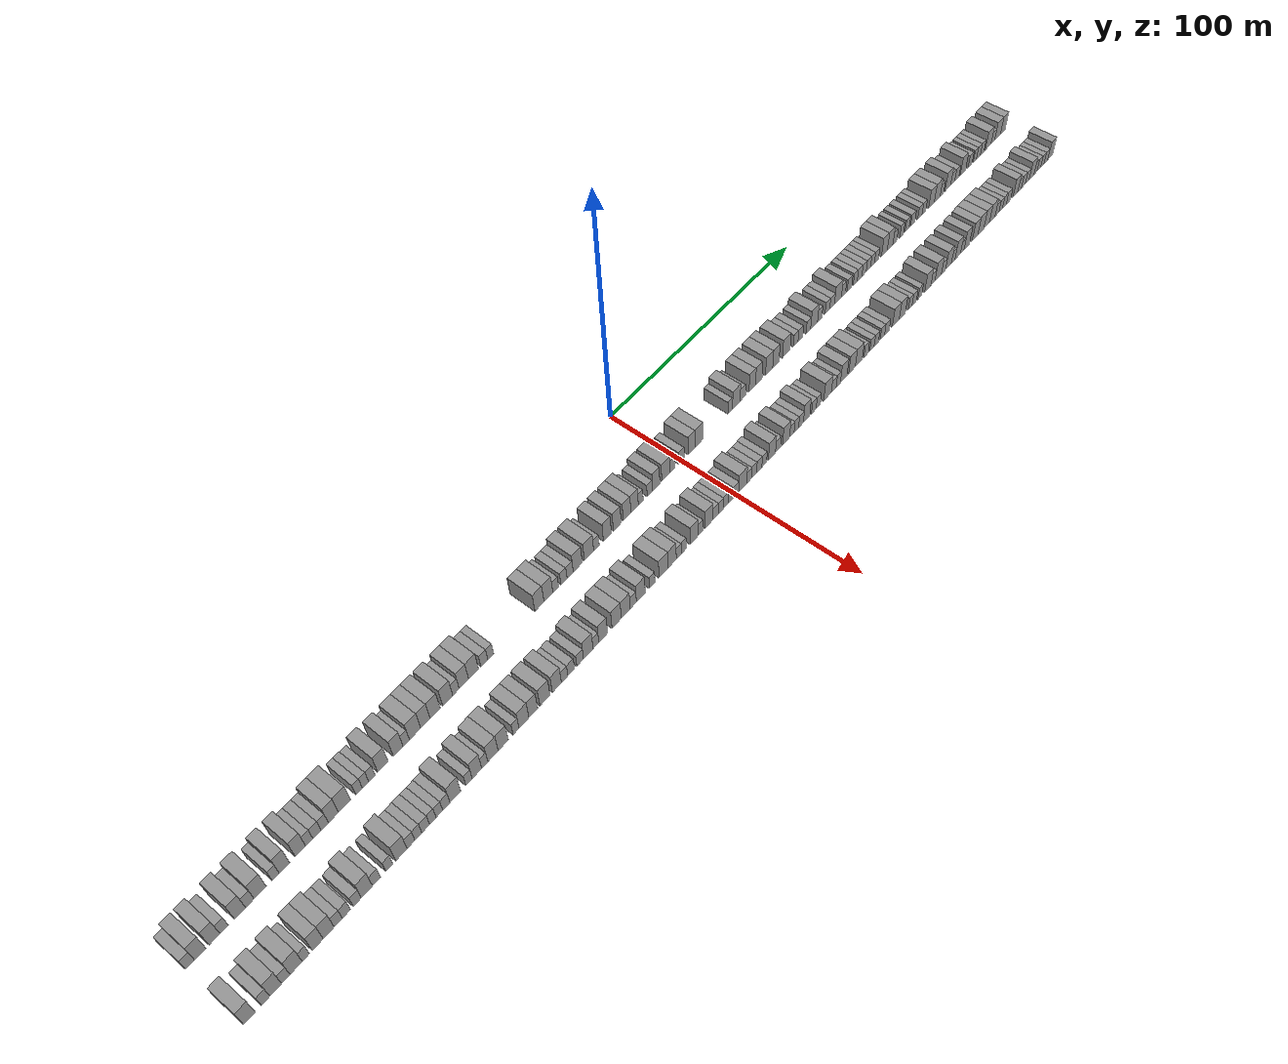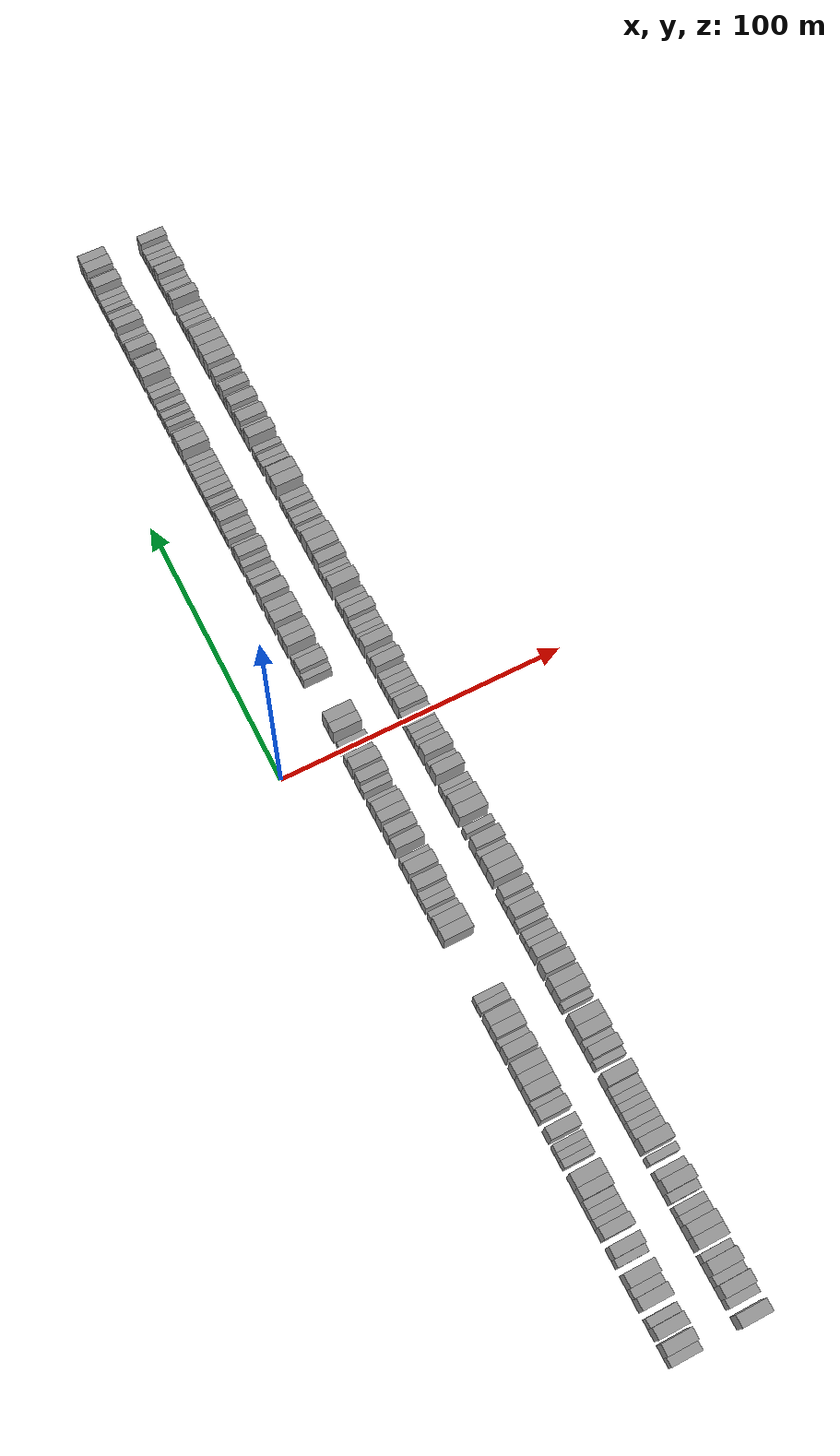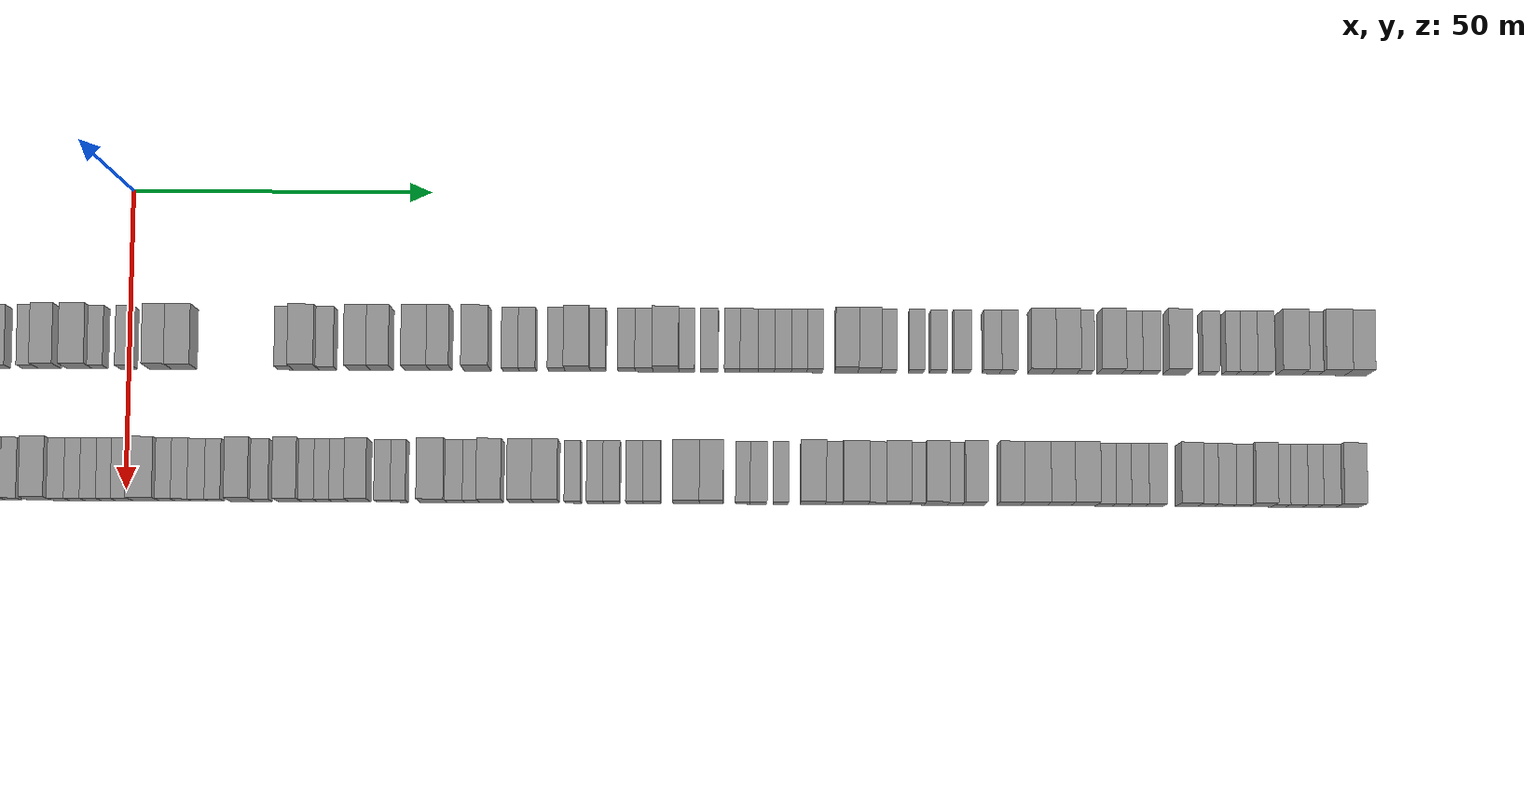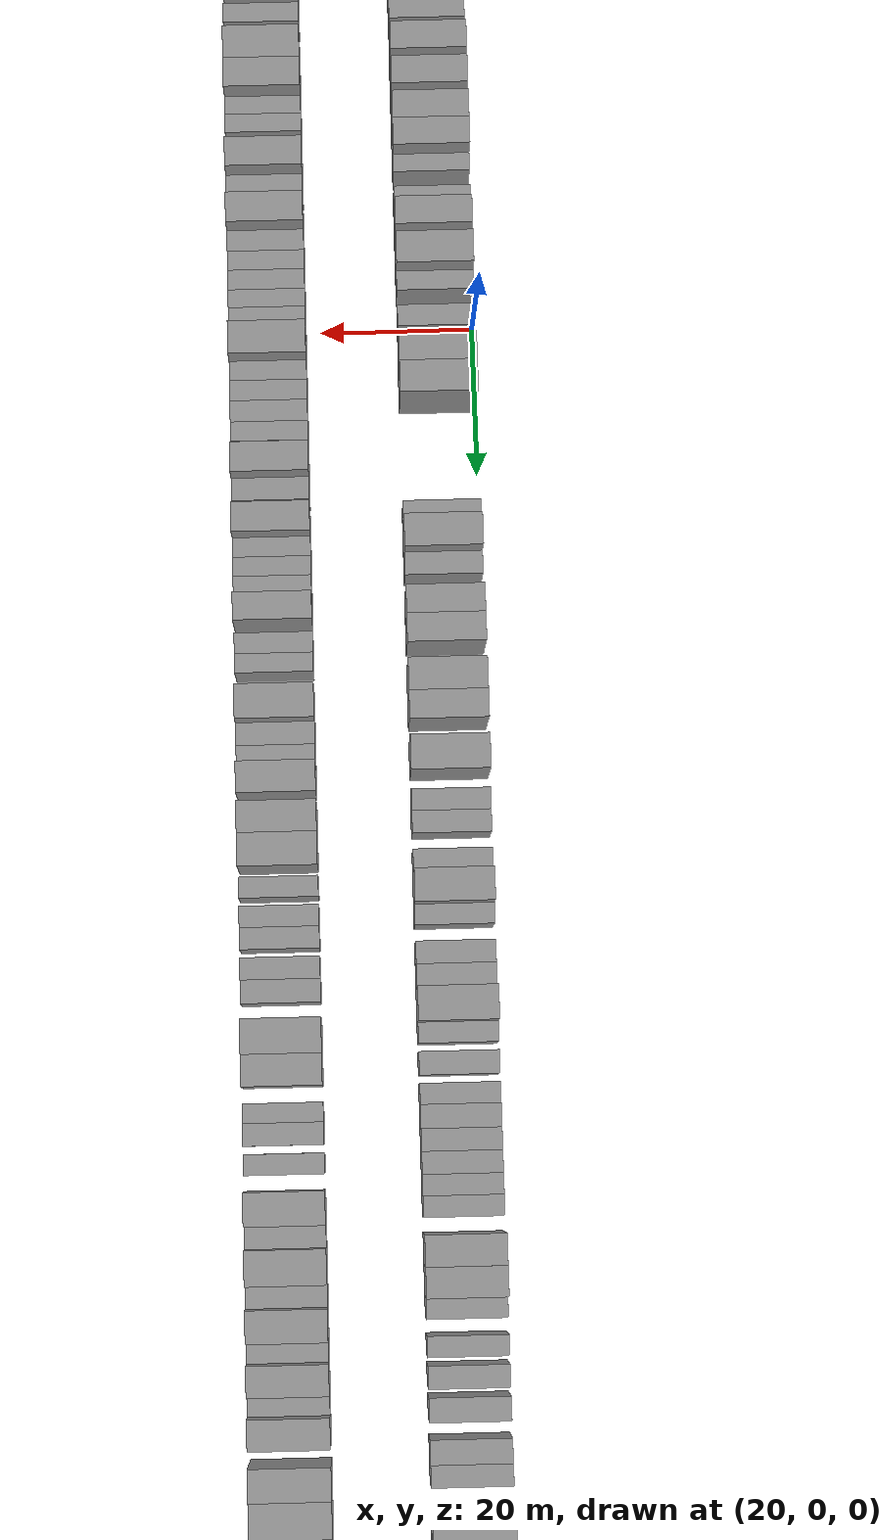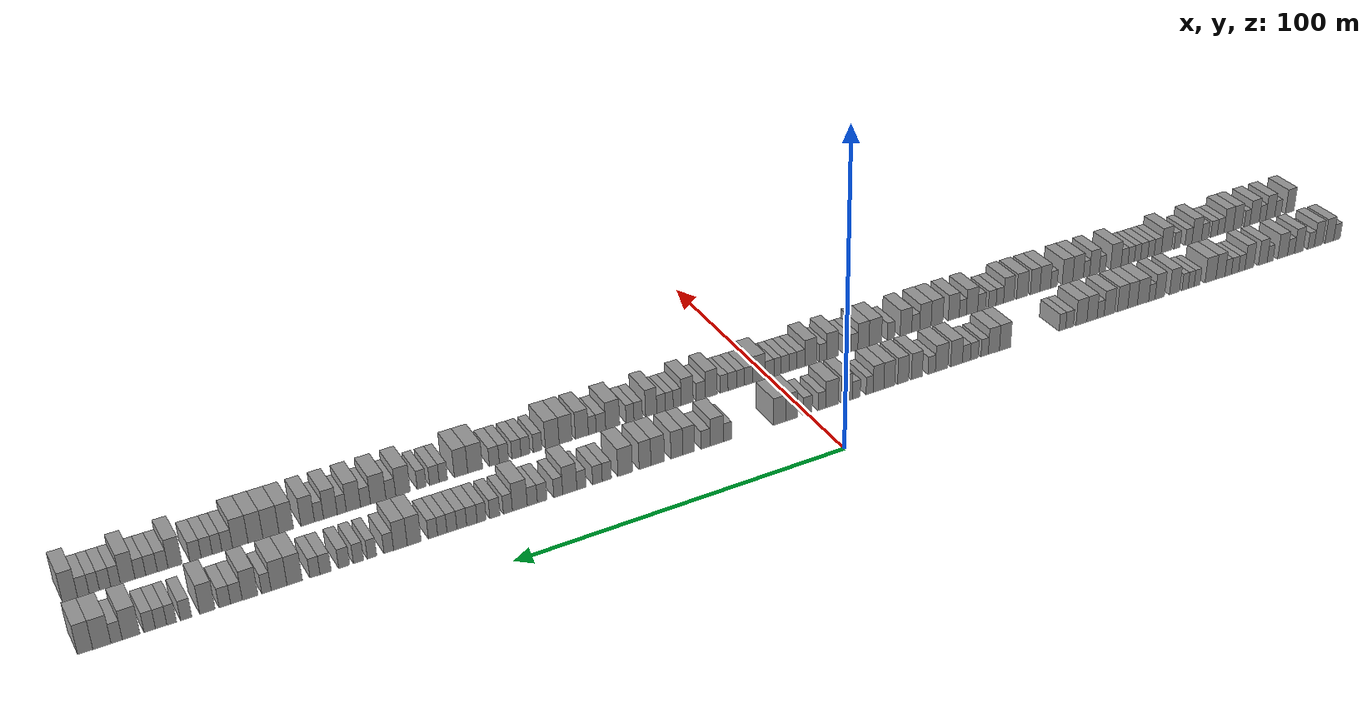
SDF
<sdf version="1.6">
 <world name="default">
  <scene>
   <sky><clouds><speed>12</speed></clouds></sky>
   <ambient>0.4 0.4 0.4 1</ambient>
   <background>0.7 0.7 0.7 1</background>
   <shadows>1</shadows>
  </scene>
  <gravity>0 0 -9.8066</gravity>
  <magnetic_field>6e-06 2.3e-05 -4.2e-05</magnetic_field>
  <physics default="0" name="default_physics" type="ode">
   <ode>
    <solver>
     <type>quick</type>
     <iters>10</iters>
     <sor>1.0</sor>
     <use_dynamic_moi_rescaling>0</use_dynamic_moi_rescaling>
    </solver>
    <constraints>
     <cfm>0</cfm>
     <erp>0.2</erp>
     <contact_max_correcting_vel>100</contact_max_correcting_vel>
     <contact_surface_layer>0.001</contact_surface_layer>
    </constraints>
   </ode>
   <max_step_size>0.004</max_step_size>
   <real_time_factor>1</real_time_factor>
   <real_time_update_rate>250</real_time_update_rate>
  </physics>
  <light name="sun" type="directional">
   <pose>0 0 10 0 0 0</pose>
   <diffuse>0.8 0.8 0.8 1</diffuse>
   <specular>0.2 0.2 0.2 1</specular>
   <attenuation>
    <range>1000</range>
    <constant>0.9</constant>
    <linear>0.01</linear>
    <quadratic>0.001</quadratic>
   </attenuation>
   <direction>-0.5 0.1 -0.9</direction>
  </light>
  <model name="building_1">
   <static>1</static>
   <pose>25.0000 -202.5292 0 0.000000 0.000000 0.000000</pose>
   <link name="link">
    <pose>0 0 3.00 0 0 0</pose>
    <collision name="collision"><geometry><box><size>10.0000 2.9416 6.0000</size></box></geometry></collision>
    <visual name="visual">
     <cast_shadows>0</cast_shadows>
     <geometry><box><size>10.0000 2.9416 6.0000</size></box></geometry>
     <material>
      <script>
       <uri>model://grey_wall/materials/scripts</uri>
       <uri>model://grey_wall/materials/textures</uri>
       <name>vrc/grey_wall</name>
      </script>
     </material>
    </visual>
   </link>
  </model>
  <model name="building_2">
   <static>1</static>
   <pose>25.0000 -199.1781 0 0.000000 0.000000 0.000000</pose>
   <link name="link">
    <pose>0 0 4.50 0 0 0</pose>
    <collision name="collision"><geometry><box><size>10.0000 3.7606 9.0000</size></box></geometry></collision>
    <visual name="visual">
     <cast_shadows>0</cast_shadows>
     <geometry><box><size>10.0000 3.7606 9.0000</size></box></geometry>
     <material>
      <script>
       <uri>model://grey_wall/materials/scripts</uri>
       <uri>model://grey_wall/materials/textures</uri>
       <name>vrc/grey_wall</name>
      </script>
     </material>
    </visual>
   </link>
  </model>
  <model name="building_3">
   <static>1</static>
   <pose>25.0000 -194.4770 0 0.000000 0.000000 0.000000</pose>
   <link name="link">
    <pose>0 0 4.50 0 0 0</pose>
    <collision name="collision"><geometry><box><size>10.0000 3.6417 9.0000</size></box></geometry></collision>
    <visual name="visual">
     <cast_shadows>0</cast_shadows>
     <geometry><box><size>10.0000 3.6417 9.0000</size></box></geometry>
     <material>
      <script>
       <uri>model://grey_wall/materials/scripts</uri>
       <uri>model://grey_wall/materials/textures</uri>
       <name>vrc/grey_wall</name>
      </script>
     </material>
    </visual>
   </link>
  </model>
  <model name="building_4">
   <static>1</static>
   <pose>25.0000 -191.2516 0 0.000000 0.000000 0.000000</pose>
   <link name="link">
    <pose>0 0 3.00 0 0 0</pose>
    <collision name="collision"><geometry><box><size>10.0000 2.8091 6.0000</size></box></geometry></collision>
    <visual name="visual">
     <cast_shadows>0</cast_shadows>
     <geometry><box><size>10.0000 2.8091 6.0000</size></box></geometry>
     <material>
      <script>
       <uri>model://grey_wall/materials/scripts</uri>
       <uri>model://grey_wall/materials/textures</uri>
       <name>vrc/grey_wall</name>
      </script>
     </material>
    </visual>
   </link>
  </model>
  <model name="building_5">
   <static>1</static>
   <pose>25.0000 -185.9650 0 0.000000 0.000000 0.000000</pose>
   <link name="link">
    <pose>0 0 4.50 0 0 0</pose>
    <collision name="collision"><geometry><box><size>10.0000 3.7642 9.0000</size></box></geometry></collision>
    <visual name="visual">
     <cast_shadows>0</cast_shadows>
     <geometry><box><size>10.0000 3.7642 9.0000</size></box></geometry>
     <material>
      <script>
       <uri>model://grey_wall/materials/scripts</uri>
       <uri>model://grey_wall/materials/textures</uri>
       <name>vrc/grey_wall</name>
      </script>
     </material>
    </visual>
   </link>
  </model>
  <model name="building_6">
   <static>1</static>
   <pose>25.0000 -182.6085 0 0.000000 0.000000 0.000000</pose>
   <link name="link">
    <pose>0 0 3.00 0 0 0</pose>
    <collision name="collision"><geometry><box><size>10.0000 2.9489 6.0000</size></box></geometry></collision>
    <visual name="visual">
     <cast_shadows>0</cast_shadows>
     <geometry><box><size>10.0000 2.9489 6.0000</size></box></geometry>
     <material>
      <script>
       <uri>model://grey_wall/materials/scripts</uri>
       <uri>model://grey_wall/materials/textures</uri>
       <name>vrc/grey_wall</name>
      </script>
     </material>
    </visual>
   </link>
  </model>
  <model name="building_7">
   <static>1</static>
   <pose>25.0000 -179.0327 0 0.000000 0.000000 0.000000</pose>
   <link name="link">
    <pose>0 0 4.50 0 0 0</pose>
    <collision name="collision"><geometry><box><size>10.0000 4.2026 9.0000</size></box></geometry></collision>
    <visual name="visual">
     <cast_shadows>0</cast_shadows>
     <geometry><box><size>10.0000 4.2026 9.0000</size></box></geometry>
     <material>
      <script>
       <uri>model://grey_wall/materials/scripts</uri>
       <uri>model://grey_wall/materials/textures</uri>
       <name>vrc/grey_wall</name>
      </script>
     </material>
    </visual>
   </link>
  </model>
  <model name="building_8">
   <static>1</static>
   <pose>25.0000 -173.6945 0 0.000000 0.000000 0.000000</pose>
   <link name="link">
    <pose>0 0 3.00 0 0 0</pose>
    <collision name="collision"><geometry><box><size>10.0000 2.4739 6.0000</size></box></geometry></collision>
    <visual name="visual">
     <cast_shadows>0</cast_shadows>
     <geometry><box><size>10.0000 2.4739 6.0000</size></box></geometry>
     <material>
      <script>
       <uri>model://grey_wall/materials/scripts</uri>
       <uri>model://grey_wall/materials/textures</uri>
       <name>vrc/grey_wall</name>
      </script>
     </material>
    </visual>
   </link>
  </model>
  <model name="building_9">
   <static>1</static>
   <pose>25.0000 -170.6190 0 0.000000 0.000000 0.000000</pose>
   <link name="link">
    <pose>0 0 4.50 0 0 0</pose>
    <collision name="collision"><geometry><box><size>10.0000 3.6771 9.0000</size></box></geometry></collision>
    <visual name="visual">
     <cast_shadows>0</cast_shadows>
     <geometry><box><size>10.0000 3.6771 9.0000</size></box></geometry>
     <material>
      <script>
       <uri>model://grey_wall/materials/scripts</uri>
       <uri>model://grey_wall/materials/textures</uri>
       <name>vrc/grey_wall</name>
      </script>
     </material>
    </visual>
   </link>
  </model>
  <model name="building_10">
   <static>1</static>
   <pose>25.0000 -164.9156 0 0.000000 0.000000 0.000000</pose>
   <link name="link">
    <pose>0 0 4.50 0 0 0</pose>
    <collision name="collision"><geometry><box><size>10.0000 3.7297 9.0000</size></box></geometry></collision>
    <visual name="visual">
     <cast_shadows>0</cast_shadows>
     <geometry><box><size>10.0000 3.7297 9.0000</size></box></geometry>
     <material>
      <script>
       <uri>model://grey_wall/materials/scripts</uri>
       <uri>model://grey_wall/materials/textures</uri>
       <name>vrc/grey_wall</name>
      </script>
     </material>
    </visual>
   </link>
  </model>
  <model name="building_11">
   <static>1</static>
   <pose>25.0000 -161.7470 0 0.000000 0.000000 0.000000</pose>
   <link name="link">
    <pose>0 0 3.00 0 0 0</pose>
    <collision name="collision"><geometry><box><size>10.0000 2.6075 6.0000</size></box></geometry></collision>
    <visual name="visual">
     <cast_shadows>0</cast_shadows>
     <geometry><box><size>10.0000 2.6075 6.0000</size></box></geometry>
     <material>
      <script>
       <uri>model://grey_wall/materials/scripts</uri>
       <uri>model://grey_wall/materials/textures</uri>
       <name>vrc/grey_wall</name>
      </script>
     </material>
    </visual>
   </link>
  </model>
  <model name="building_12">
   <static>1</static>
   <pose>25.0000 -158.9450 0 0.000000 0.000000 0.000000</pose>
   <link name="link">
    <pose>0 0 3.00 0 0 0</pose>
    <collision name="collision"><geometry><box><size>10.0000 2.9965 6.0000</size></box></geometry></collision>
    <visual name="visual">
     <cast_shadows>0</cast_shadows>
     <geometry><box><size>10.0000 2.9965 6.0000</size></box></geometry>
     <material>
      <script>
       <uri>model://grey_wall/materials/scripts</uri>
       <uri>model://grey_wall/materials/textures</uri>
       <name>vrc/grey_wall</name>
      </script>
     </material>
    </visual>
   </link>
  </model>
  <model name="building_13">
   <static>1</static>
   <pose>25.0000 -156.1276 0 0.000000 0.000000 0.000000</pose>
   <link name="link">
    <pose>0 0 3.00 0 0 0</pose>
    <collision name="collision"><geometry><box><size>10.0000 2.6382 6.0000</size></box></geometry></collision>
    <visual name="visual">
     <cast_shadows>0</cast_shadows>
     <geometry><box><size>10.0000 2.6382 6.0000</size></box></geometry>
     <material>
      <script>
       <uri>model://grey_wall/materials/scripts</uri>
       <uri>model://grey_wall/materials/textures</uri>
       <name>vrc/grey_wall</name>
      </script>
     </material>
    </visual>
   </link>
  </model>
  <model name="building_14">
   <static>1</static>
   <pose>25.0000 -152.9464 0 0.000000 0.000000 0.000000</pose>
   <link name="link">
    <pose>0 0 4.50 0 0 0</pose>
    <collision name="collision"><geometry><box><size>10.0000 3.7243 9.0000</size></box></geometry></collision>
    <visual name="visual">
     <cast_shadows>0</cast_shadows>
     <geometry><box><size>10.0000 3.7243 9.0000</size></box></geometry>
     <material>
      <script>
       <uri>model://grey_wall/materials/scripts</uri>
       <uri>model://grey_wall/materials/textures</uri>
       <name>vrc/grey_wall</name>
      </script>
     </material>
    </visual>
   </link>
  </model>
  <model name="building_15">
   <static>1</static>
   <pose>25.0000 -148.8476 0 0.000000 0.000000 0.000000</pose>
   <link name="link">
    <pose>0 0 4.50 0 0 0</pose>
    <collision name="collision"><geometry><box><size>10.0000 4.4733 9.0000</size></box></geometry></collision>
    <visual name="visual">
     <cast_shadows>0</cast_shadows>
     <geometry><box><size>10.0000 4.4733 9.0000</size></box></geometry>
     <material>
      <script>
       <uri>model://grey_wall/materials/scripts</uri>
       <uri>model://grey_wall/materials/textures</uri>
       <name>vrc/grey_wall</name>
      </script>
     </material>
    </visual>
   </link>
  </model>
  <model name="building_16">
   <static>1</static>
   <pose>25.0000 -143.3843 0 0.000000 0.000000 0.000000</pose>
   <link name="link">
    <pose>0 0 3.00 0 0 0</pose>
    <collision name="collision"><geometry><box><size>10.0000 2.4534 6.0000</size></box></geometry></collision>
    <visual name="visual">
     <cast_shadows>0</cast_shadows>
     <geometry><box><size>10.0000 2.4534 6.0000</size></box></geometry>
     <material>
      <script>
       <uri>model://grey_wall/materials/scripts</uri>
       <uri>model://grey_wall/materials/textures</uri>
       <name>vrc/grey_wall</name>
      </script>
     </material>
    </visual>
   </link>
  </model>
  <model name="building_17">
   <static>1</static>
   <pose>25.0000 -140.9417 0 0.000000 0.000000 0.000000</pose>
   <link name="link">
    <pose>0 0 3.00 0 0 0</pose>
    <collision name="collision"><geometry><box><size>10.0000 2.4318 6.0000</size></box></geometry></collision>
    <visual name="visual">
     <cast_shadows>0</cast_shadows>
     <geometry><box><size>10.0000 2.4318 6.0000</size></box></geometry>
     <material>
      <script>
       <uri>model://grey_wall/materials/scripts</uri>
       <uri>model://grey_wall/materials/textures</uri>
       <name>vrc/grey_wall</name>
      </script>
     </material>
    </visual>
   </link>
  </model>
  <model name="building_18">
   <static>1</static>
   <pose>25.0000 -138.5001 0 0.000000 0.000000 0.000000</pose>
   <link name="link">
    <pose>0 0 3.00 0 0 0</pose>
    <collision name="collision"><geometry><box><size>10.0000 2.4512 6.0000</size></box></geometry></collision>
    <visual name="visual">
     <cast_shadows>0</cast_shadows>
     <geometry><box><size>10.0000 2.4512 6.0000</size></box></geometry>
     <material>
      <script>
       <uri>model://grey_wall/materials/scripts</uri>
       <uri>model://grey_wall/materials/textures</uri>
       <name>vrc/grey_wall</name>
      </script>
     </material>
    </visual>
   </link>
  </model>
  <model name="building_19">
   <static>1</static>
   <pose>25.0000 -134.2684 0 0.000000 0.000000 0.000000</pose>
   <link name="link">
    <pose>0 0 4.50 0 0 0</pose>
    <collision name="collision"><geometry><box><size>10.0000 4.0122 9.0000</size></box></geometry></collision>
    <visual name="visual">
     <cast_shadows>0</cast_shadows>
     <geometry><box><size>10.0000 4.0122 9.0000</size></box></geometry>
     <material>
      <script>
       <uri>model://grey_wall/materials/scripts</uri>
       <uri>model://grey_wall/materials/textures</uri>
       <name>vrc/grey_wall</name>
      </script>
     </material>
    </visual>
   </link>
  </model>
  <model name="building_20">
   <static>1</static>
   <pose>25.0000 -128.3569 0 0.000000 0.000000 0.000000</pose>
   <link name="link">
    <pose>0 0 4.50 0 0 0</pose>
    <collision name="collision"><geometry><box><size>10.0000 3.8109 9.0000</size></box></geometry></collision>
    <visual name="visual">
     <cast_shadows>0</cast_shadows>
     <geometry><box><size>10.0000 3.8109 9.0000</size></box></geometry>
     <material>
      <script>
       <uri>model://grey_wall/materials/scripts</uri>
       <uri>model://grey_wall/materials/textures</uri>
       <name>vrc/grey_wall</name>
      </script>
     </material>
    </visual>
   </link>
  </model>
  <model name="building_21">
   <static>1</static>
   <pose>25.0000 -125.1883 0 0.000000 0.000000 0.000000</pose>
   <link name="link">
    <pose>0 0 3.00 0 0 0</pose>
    <collision name="collision"><geometry><box><size>10.0000 2.5262 6.0000</size></box></geometry></collision>
    <visual name="visual">
     <cast_shadows>0</cast_shadows>
     <geometry><box><size>10.0000 2.5262 6.0000</size></box></geometry>
     <material>
      <script>
       <uri>model://grey_wall/materials/scripts</uri>
       <uri>model://grey_wall/materials/textures</uri>
       <name>vrc/grey_wall</name>
      </script>
     </material>
    </visual>
   </link>
  </model>
  <model name="building_22">
   <static>1</static>
   <pose>25.0000 -121.6837 0 0.000000 0.000000 0.000000</pose>
   <link name="link">
    <pose>0 0 4.50 0 0 0</pose>
    <collision name="collision"><geometry><box><size>10.0000 4.4832 9.0000</size></box></geometry></collision>
    <visual name="visual">
     <cast_shadows>0</cast_shadows>
     <geometry><box><size>10.0000 4.4832 9.0000</size></box></geometry>
     <material>
      <script>
       <uri>model://grey_wall/materials/scripts</uri>
       <uri>model://grey_wall/materials/textures</uri>
       <name>vrc/grey_wall</name>
      </script>
     </material>
    </visual>
   </link>
  </model>
  <model name="building_23">
   <static>1</static>
   <pose>25.0000 -117.5654 0 0.000000 0.000000 0.000000</pose>
   <link name="link">
    <pose>0 0 4.50 0 0 0</pose>
    <collision name="collision"><geometry><box><size>10.0000 3.7533 9.0000</size></box></geometry></collision>
    <visual name="visual">
     <cast_shadows>0</cast_shadows>
     <geometry><box><size>10.0000 3.7533 9.0000</size></box></geometry>
     <material>
      <script>
       <uri>model://grey_wall/materials/scripts</uri>
       <uri>model://grey_wall/materials/textures</uri>
       <name>vrc/grey_wall</name>
      </script>
     </material>
    </visual>
   </link>
  </model>
  <model name="building_24">
   <static>1</static>
   <pose>25.0000 -113.6408 0 0.000000 0.000000 0.000000</pose>
   <link name="link">
    <pose>0 0 4.50 0 0 0</pose>
    <collision name="collision"><geometry><box><size>10.0000 4.0959 9.0000</size></box></geometry></collision>
    <visual name="visual">
     <cast_shadows>0</cast_shadows>
     <geometry><box><size>10.0000 4.0959 9.0000</size></box></geometry>
     <material>
      <script>
       <uri>model://grey_wall/materials/scripts</uri>
       <uri>model://grey_wall/materials/textures</uri>
       <name>vrc/grey_wall</name>
      </script>
     </material>
    </visual>
   </link>
  </model>
  <model name="building_25">
   <static>1</static>
   <pose>25.0000 -108.5217 0 0.000000 0.000000 0.000000</pose>
   <link name="link">
    <pose>0 0 4.50 0 0 0</pose>
    <collision name="collision"><geometry><box><size>10.0000 4.1422 9.0000</size></box></geometry></collision>
    <visual name="visual">
     <cast_shadows>0</cast_shadows>
     <geometry><box><size>10.0000 4.1422 9.0000</size></box></geometry>
     <material>
      <script>
       <uri>model://grey_wall/materials/scripts</uri>
       <uri>model://grey_wall/materials/textures</uri>
       <name>vrc/grey_wall</name>
      </script>
     </material>
    </visual>
   </link>
  </model>
  <model name="building_26">
   <static>1</static>
   <pose>25.0000 -105.1016 0 0.000000 0.000000 0.000000</pose>
   <link name="link">
    <pose>0 0 3.00 0 0 0</pose>
    <collision name="collision"><geometry><box><size>10.0000 2.6979 6.0000</size></box></geometry></collision>
    <visual name="visual">
     <cast_shadows>0</cast_shadows>
     <geometry><box><size>10.0000 2.6979 6.0000</size></box></geometry>
     <material>
      <script>
       <uri>model://grey_wall/materials/scripts</uri>
       <uri>model://grey_wall/materials/textures</uri>
       <name>vrc/grey_wall</name>
      </script>
     </material>
    </visual>
   </link>
  </model>
  <model name="building_27">
   <static>1</static>
   <pose>25.0000 -101.7893 0 0.000000 0.000000 0.000000</pose>
   <link name="link">
    <pose>0 0 4.50 0 0 0</pose>
    <collision name="collision"><geometry><box><size>10.0000 3.9268 9.0000</size></box></geometry></collision>
    <visual name="visual">
     <cast_shadows>0</cast_shadows>
     <geometry><box><size>10.0000 3.9268 9.0000</size></box></geometry>
     <material>
      <script>
       <uri>model://grey_wall/materials/scripts</uri>
       <uri>model://grey_wall/materials/textures</uri>
       <name>vrc/grey_wall</name>
      </script>
     </material>
    </visual>
   </link>
  </model>
  <model name="building_28">
   <static>1</static>
   <pose>25.0000 -97.7386 0 0.000000 0.000000 0.000000</pose>
   <link name="link">
    <pose>0 0 4.50 0 0 0</pose>
    <collision name="collision"><geometry><box><size>10.0000 4.1745 9.0000</size></box></geometry></collision>
    <visual name="visual">
     <cast_shadows>0</cast_shadows>
     <geometry><box><size>10.0000 4.1745 9.0000</size></box></geometry>
     <material>
      <script>
       <uri>model://grey_wall/materials/scripts</uri>
       <uri>model://grey_wall/materials/textures</uri>
       <name>vrc/grey_wall</name>
      </script>
     </material>
    </visual>
   </link>
  </model>
  <model name="building_29">
   <static>1</static>
   <pose>25.0000 -93.1996 0 0.000000 0.000000 0.000000</pose>
   <link name="link">
    <pose>0 0 3.00 0 0 0</pose>
    <collision name="collision"><geometry><box><size>10.0000 2.9034 6.0000</size></box></geometry></collision>
    <visual name="visual">
     <cast_shadows>0</cast_shadows>
     <geometry><box><size>10.0000 2.9034 6.0000</size></box></geometry>
     <material>
      <script>
       <uri>model://grey_wall/materials/scripts</uri>
       <uri>model://grey_wall/materials/textures</uri>
       <name>vrc/grey_wall</name>
      </script>
     </material>
    </visual>
   </link>
  </model>
  <model name="building_30">
   <static>1</static>
   <pose>25.0000 -90.4950 0 0.000000 0.000000 0.000000</pose>
   <link name="link">
    <pose>0 0 3.00 0 0 0</pose>
    <collision name="collision"><geometry><box><size>10.0000 2.5059 6.0000</size></box></geometry></collision>
    <visual name="visual">
     <cast_shadows>0</cast_shadows>
     <geometry><box><size>10.0000 2.5059 6.0000</size></box></geometry>
     <material>
      <script>
       <uri>model://grey_wall/materials/scripts</uri>
       <uri>model://grey_wall/materials/textures</uri>
       <name>vrc/grey_wall</name>
      </script>
     </material>
    </visual>
   </link>
  </model>
  <model name="building_31">
   <static>1</static>
   <pose>25.0000 -69.0618 0 0.000000 0.000000 0.000000</pose>
   <link name="link">
    <pose>0 0 4.50 0 0 0</pose>
    <collision name="collision"><geometry><box><size>10.0000 4.1202 9.0000</size></box></geometry></collision>
    <visual name="visual">
     <cast_shadows>0</cast_shadows>
     <geometry><box><size>10.0000 4.1202 9.0000</size></box></geometry>
     <material>
      <script>
       <uri>model://grey_wall/materials/scripts</uri>
       <uri>model://grey_wall/materials/textures</uri>
       <name>vrc/grey_wall</name>
      </script>
     </material>
    </visual>
   </link>
  </model>
  <model name="building_32">
   <static>1</static>
   <pose>25.0000 -64.9716 0 0.000000 0.000000 0.000000</pose>
   <link name="link">
    <pose>0 0 4.50 0 0 0</pose>
    <collision name="collision"><geometry><box><size>10.0000 4.0602 9.0000</size></box></geometry></collision>
    <visual name="visual">
     <cast_shadows>0</cast_shadows>
     <geometry><box><size>10.0000 4.0602 9.0000</size></box></geometry>
     <material>
      <script>
       <uri>model://grey_wall/materials/scripts</uri>
       <uri>model://grey_wall/materials/textures</uri>
       <name>vrc/grey_wall</name>
      </script>
     </material>
    </visual>
   </link>
  </model>
  <model name="building_33">
   <static>1</static>
   <pose>25.0000 -61.6120 0 0.000000 0.000000 0.000000</pose>
   <link name="link">
    <pose>0 0 3.00 0 0 0</pose>
    <collision name="collision"><geometry><box><size>10.0000 2.6590 6.0000</size></box></geometry></collision>
    <visual name="visual">
     <cast_shadows>0</cast_shadows>
     <geometry><box><size>10.0000 2.6590 6.0000</size></box></geometry>
     <material>
      <script>
       <uri>model://grey_wall/materials/scripts</uri>
       <uri>model://grey_wall/materials/textures</uri>
       <name>vrc/grey_wall</name>
      </script>
     </material>
    </visual>
   </link>
  </model>
  <model name="building_34">
   <static>1</static>
   <pose>25.0000 -57.8716 0 0.000000 0.000000 0.000000</pose>
   <link name="link">
    <pose>0 0 3.00 0 0 0</pose>
    <collision name="collision"><geometry><box><size>10.0000 2.8217 6.0000</size></box></geometry></collision>
    <visual name="visual">
     <cast_shadows>0</cast_shadows>
     <geometry><box><size>10.0000 2.8217 6.0000</size></box></geometry>
     <material>
      <script>
       <uri>model://grey_wall/materials/scripts</uri>
       <uri>model://grey_wall/materials/textures</uri>
       <name>vrc/grey_wall</name>
      </script>
     </material>
    </visual>
   </link>
  </model>
  <model name="building_35">
   <static>1</static>
   <pose>25.0000 -55.0200 0 0.000000 0.000000 0.000000</pose>
   <link name="link">
    <pose>0 0 3.00 0 0 0</pose>
    <collision name="collision"><geometry><box><size>10.0000 2.8814 6.0000</size></box></geometry></collision>
    <visual name="visual">
     <cast_shadows>0</cast_shadows>
     <geometry><box><size>10.0000 2.8814 6.0000</size></box></geometry>
     <material>
      <script>
       <uri>model://grey_wall/materials/scripts</uri>
       <uri>model://grey_wall/materials/textures</uri>
       <name>vrc/grey_wall</name>
      </script>
     </material>
    </visual>
   </link>
  </model>
  <model name="building_36">
   <static>1</static>
   <pose>25.0000 -51.4653 0 0.000000 0.000000 0.000000</pose>
   <link name="link">
    <pose>0 0 4.50 0 0 0</pose>
    <collision name="collision"><geometry><box><size>10.0000 4.2280 9.0000</size></box></geometry></collision>
    <visual name="visual">
     <cast_shadows>0</cast_shadows>
     <geometry><box><size>10.0000 4.2280 9.0000</size></box></geometry>
     <material>
      <script>
       <uri>model://grey_wall/materials/scripts</uri>
       <uri>model://grey_wall/materials/textures</uri>
       <name>vrc/grey_wall</name>
      </script>
     </material>
    </visual>
   </link>
  </model>
  <model name="building_37">
   <static>1</static>
   <pose>25.0000 -46.1372 0 0.000000 0.000000 0.000000</pose>
   <link name="link">
    <pose>0 0 4.50 0 0 0</pose>
    <collision name="collision"><geometry><box><size>10.0000 4.4281 9.0000</size></box></geometry></collision>
    <visual name="visual">
     <cast_shadows>0</cast_shadows>
     <geometry><box><size>10.0000 4.4281 9.0000</size></box></geometry>
     <material>
      <script>
       <uri>model://grey_wall/materials/scripts</uri>
       <uri>model://grey_wall/materials/textures</uri>
       <name>vrc/grey_wall</name>
      </script>
     </material>
    </visual>
   </link>
  </model>
  <model name="building_38">
   <static>1</static>
   <pose>25.0000 -42.6079 0 0.000000 0.000000 0.000000</pose>
   <link name="link">
    <pose>0 0 3.00 0 0 0</pose>
    <collision name="collision"><geometry><box><size>10.0000 2.6304 6.0000</size></box></geometry></collision>
    <visual name="visual">
     <cast_shadows>0</cast_shadows>
     <geometry><box><size>10.0000 2.6304 6.0000</size></box></geometry>
     <material>
      <script>
       <uri>model://grey_wall/materials/scripts</uri>
       <uri>model://grey_wall/materials/textures</uri>
       <name>vrc/grey_wall</name>
      </script>
     </material>
    </visual>
   </link>
  </model>
  <model name="building_39">
   <static>1</static>
   <pose>25.0000 -37.3734 0 0.000000 0.000000 0.000000</pose>
   <link name="link">
    <pose>0 0 4.50 0 0 0</pose>
    <collision name="collision"><geometry><box><size>10.0000 3.8386 9.0000</size></box></geometry></collision>
    <visual name="visual">
     <cast_shadows>0</cast_shadows>
     <geometry><box><size>10.0000 3.8386 9.0000</size></box></geometry>
     <material>
      <script>
       <uri>model://grey_wall/materials/scripts</uri>
       <uri>model://grey_wall/materials/textures</uri>
       <name>vrc/grey_wall</name>
      </script>
     </material>
    </visual>
   </link>
  </model>
  <model name="building_40">
   <static>1</static>
   <pose>25.0000 -32.5507 0 0.000000 0.000000 0.000000</pose>
   <link name="link">
    <pose>0 0 4.50 0 0 0</pose>
    <collision name="collision"><geometry><box><size>10.0000 3.8069 9.0000</size></box></geometry></collision>
    <visual name="visual">
     <cast_shadows>0</cast_shadows>
     <geometry><box><size>10.0000 3.8069 9.0000</size></box></geometry>
     <material>
      <script>
       <uri>model://grey_wall/materials/scripts</uri>
       <uri>model://grey_wall/materials/textures</uri>
       <name>vrc/grey_wall</name>
      </script>
     </material>
    </visual>
   </link>
  </model>
  <model name="building_41">
   <static>1</static>
   <pose>25.0000 -27.7635 0 0.000000 0.000000 0.000000</pose>
   <link name="link">
    <pose>0 0 4.50 0 0 0</pose>
    <collision name="collision"><geometry><box><size>10.0000 3.7676 9.0000</size></box></geometry></collision>
    <visual name="visual">
     <cast_shadows>0</cast_shadows>
     <geometry><box><size>10.0000 3.7676 9.0000</size></box></geometry>
     <material>
      <script>
       <uri>model://grey_wall/materials/scripts</uri>
       <uri>model://grey_wall/materials/textures</uri>
       <name>vrc/grey_wall</name>
      </script>
     </material>
    </visual>
   </link>
  </model>
  <model name="building_42">
   <static>1</static>
   <pose>25.0000 -24.0283 0 0.000000 0.000000 0.000000</pose>
   <link name="link">
    <pose>0 0 4.50 0 0 0</pose>
    <collision name="collision"><geometry><box><size>10.0000 3.7028 9.0000</size></box></geometry></collision>
    <visual name="visual">
     <cast_shadows>0</cast_shadows>
     <geometry><box><size>10.0000 3.7028 9.0000</size></box></geometry>
     <material>
      <script>
       <uri>model://grey_wall/materials/scripts</uri>
       <uri>model://grey_wall/materials/textures</uri>
       <name>vrc/grey_wall</name>
      </script>
     </material>
    </visual>
   </link>
  </model>
  <model name="building_43">
   <static>1</static>
   <pose>25.0000 -20.9685 0 0.000000 0.000000 0.000000</pose>
   <link name="link">
    <pose>0 0 3.00 0 0 0</pose>
    <collision name="collision"><geometry><box><size>10.0000 2.4167 6.0000</size></box></geometry></collision>
    <visual name="visual">
     <cast_shadows>0</cast_shadows>
     <geometry><box><size>10.0000 2.4167 6.0000</size></box></geometry>
     <material>
      <script>
       <uri>model://grey_wall/materials/scripts</uri>
       <uri>model://grey_wall/materials/textures</uri>
       <name>vrc/grey_wall</name>
      </script>
     </material>
    </visual>
   </link>
  </model>
  <model name="building_44">
   <static>1</static>
   <pose>25.0000 -16.4239 0 0.000000 0.000000 0.000000</pose>
   <link name="link">
    <pose>0 0 3.00 0 0 0</pose>
    <collision name="collision"><geometry><box><size>10.0000 2.6726 6.0000</size></box></geometry></collision>
    <visual name="visual">
     <cast_shadows>0</cast_shadows>
     <geometry><box><size>10.0000 2.6726 6.0000</size></box></geometry>
     <material>
      <script>
       <uri>model://grey_wall/materials/scripts</uri>
       <uri>model://grey_wall/materials/textures</uri>
       <name>vrc/grey_wall</name>
      </script>
     </material>
    </visual>
   </link>
  </model>
  <model name="building_45">
   <static>1</static>
   <pose>25.0000 -13.2102 0 0.000000 0.000000 0.000000</pose>
   <link name="link">
    <pose>0 0 4.50 0 0 0</pose>
    <collision name="collision"><geometry><box><size>10.0000 3.7548 9.0000</size></box></geometry></collision>
    <visual name="visual">
     <cast_shadows>0</cast_shadows>
     <geometry><box><size>10.0000 3.7548 9.0000</size></box></geometry>
     <material>
      <script>
       <uri>model://grey_wall/materials/scripts</uri>
       <uri>model://grey_wall/materials/textures</uri>
       <name>vrc/grey_wall</name>
      </script>
     </material>
    </visual>
   </link>
  </model>
  <model name="building_46">
   <static>1</static>
   <pose>25.0000 -8.2017 0 0.000000 0.000000 0.000000</pose>
   <link name="link">
    <pose>0 0 4.50 0 0 0</pose>
    <collision name="collision"><geometry><box><size>10.0000 4.2623 9.0000</size></box></geometry></collision>
    <visual name="visual">
     <cast_shadows>0</cast_shadows>
     <geometry><box><size>10.0000 4.2623 9.0000</size></box></geometry>
     <material>
      <script>
       <uri>model://grey_wall/materials/scripts</uri>
       <uri>model://grey_wall/materials/textures</uri>
       <name>vrc/grey_wall</name>
      </script>
     </material>
    </visual>
   </link>
  </model>
  <model name="building_47">
   <static>1</static>
   <pose>25.0000 -4.7786 0 0.000000 0.000000 0.000000</pose>
   <link name="link">
    <pose>0 0 3.00 0 0 0</pose>
    <collision name="collision"><geometry><box><size>10.0000 2.5840 6.0000</size></box></geometry></collision>
    <visual name="visual">
     <cast_shadows>0</cast_shadows>
     <geometry><box><size>10.0000 2.5840 6.0000</size></box></geometry>
     <material>
      <script>
       <uri>model://grey_wall/materials/scripts</uri>
       <uri>model://grey_wall/materials/textures</uri>
       <name>vrc/grey_wall</name>
      </script>
     </material>
    </visual>
   </link>
  </model>
  <model name="building_48">
   <static>1</static>
   <pose>25.0000 -0.0581 0 0.000000 0.000000 0.000000</pose>
   <link name="link">
    <pose>0 0 3.00 0 0 0</pose>
    <collision name="collision"><geometry><box><size>10.0000 2.8570 6.0000</size></box></geometry></collision>
    <visual name="visual">
     <cast_shadows>0</cast_shadows>
     <geometry><box><size>10.0000 2.8570 6.0000</size></box></geometry>
     <material>
      <script>
       <uri>model://grey_wall/materials/scripts</uri>
       <uri>model://grey_wall/materials/textures</uri>
       <name>vrc/grey_wall</name>
      </script>
     </material>
    </visual>
   </link>
  </model>
  <model name="building_49">
   <static>1</static>
   <pose>25.0000 5.2194 0 0.000000 0.000000 0.000000</pose>
   <link name="link">
    <pose>0 0 4.50 0 0 0</pose>
    <collision name="collision"><geometry><box><size>10.0000 3.6980 9.0000</size></box></geometry></collision>
    <visual name="visual">
     <cast_shadows>0</cast_shadows>
     <geometry><box><size>10.0000 3.6980 9.0000</size></box></geometry>
     <material>
      <script>
       <uri>model://grey_wall/materials/scripts</uri>
       <uri>model://grey_wall/materials/textures</uri>
       <name>vrc/grey_wall</name>
      </script>
     </material>
    </visual>
   </link>
  </model>
  <model name="building_50">
   <static>1</static>
   <pose>25.0000 9.1772 0 0.000000 0.000000 0.000000</pose>
   <link name="link">
    <pose>0 0 4.50 0 0 0</pose>
    <collision name="collision"><geometry><box><size>10.0000 4.2176 9.0000</size></box></geometry></collision>
    <visual name="visual">
     <cast_shadows>0</cast_shadows>
     <geometry><box><size>10.0000 4.2176 9.0000</size></box></geometry>
     <material>
      <script>
       <uri>model://grey_wall/materials/scripts</uri>
       <uri>model://grey_wall/materials/textures</uri>
       <name>vrc/grey_wall</name>
      </script>
     </material>
    </visual>
   </link>
  </model>
  <model name="building_51">
   <static>1</static>
   <pose>25.0000 26.0716 0 0.000000 0.000000 0.000000</pose>
   <link name="link">
    <pose>0 0 3.00 0 0 0</pose>
    <collision name="collision"><geometry><box><size>10.0000 2.5238 6.0000</size></box></geometry></collision>
    <visual name="visual">
     <cast_shadows>0</cast_shadows>
     <geometry><box><size>10.0000 2.5238 6.0000</size></box></geometry>
     <material>
      <script>
       <uri>model://grey_wall/materials/scripts</uri>
       <uri>model://grey_wall/materials/textures</uri>
       <name>vrc/grey_wall</name>
      </script>
     </material>
    </visual>
   </link>
  </model>
  <model name="building_52">
   <static>1</static>
   <pose>25.0000 29.4768 0 0.000000 0.000000 0.000000</pose>
   <link name="link">
    <pose>0 0 4.50 0 0 0</pose>
    <collision name="collision"><geometry><box><size>10.0000 4.2866 9.0000</size></box></geometry></collision>
    <visual name="visual">
     <cast_shadows>0</cast_shadows>
     <geometry><box><size>10.0000 4.2866 9.0000</size></box></geometry>
     <material>
      <script>
       <uri>model://grey_wall/materials/scripts</uri>
       <uri>model://grey_wall/materials/textures</uri>
       <name>vrc/grey_wall</name>
      </script>
     </material>
    </visual>
   </link>
  </model>
  <model name="building_53">
   <static>1</static>
   <pose>25.0000 33.1085 0 0.000000 0.000000 0.000000</pose>
   <link name="link">
    <pose>0 0 3.00 0 0 0</pose>
    <collision name="collision"><geometry><box><size>10.0000 2.9769 6.0000</size></box></geometry></collision>
    <visual name="visual">
     <cast_shadows>0</cast_shadows>
     <geometry><box><size>10.0000 2.9769 6.0000</size></box></geometry>
     <material>
      <script>
       <uri>model://grey_wall/materials/scripts</uri>
       <uri>model://grey_wall/materials/textures</uri>
       <name>vrc/grey_wall</name>
      </script>
     </material>
    </visual>
   </link>
  </model>
  <model name="building_54">
   <static>1</static>
   <pose>25.0000 38.4390 0 0.000000 0.000000 0.000000</pose>
   <link name="link">
    <pose>0 0 4.50 0 0 0</pose>
    <collision name="collision"><geometry><box><size>10.0000 3.6842 9.0000</size></box></geometry></collision>
    <visual name="visual">
     <cast_shadows>0</cast_shadows>
     <geometry><box><size>10.0000 3.6842 9.0000</size></box></geometry>
     <material>
      <script>
       <uri>model://grey_wall/materials/scripts</uri>
       <uri>model://grey_wall/materials/textures</uri>
       <name>vrc/grey_wall</name>
      </script>
     </material>
    </visual>
   </link>
  </model>
  <model name="building_55">
   <static>1</static>
   <pose>25.0000 42.1352 0 0.000000 0.000000 0.000000</pose>
   <link name="link">
    <pose>0 0 4.50 0 0 0</pose>
    <collision name="collision"><geometry><box><size>10.0000 3.7081 9.0000</size></box></geometry></collision>
    <visual name="visual">
     <cast_shadows>0</cast_shadows>
     <geometry><box><size>10.0000 3.7081 9.0000</size></box></geometry>
     <material>
      <script>
       <uri>model://grey_wall/materials/scripts</uri>
       <uri>model://grey_wall/materials/textures</uri>
       <name>vrc/grey_wall</name>
      </script>
     </material>
    </visual>
   </link>
  </model>
  <model name="building_56">
   <static>1</static>
   <pose>25.0000 48.0854 0 0.000000 0.000000 0.000000</pose>
   <link name="link">
    <pose>0 0 4.50 0 0 0</pose>
    <collision name="collision"><geometry><box><size>10.0000 4.1924 9.0000</size></box></geometry></collision>
    <visual name="visual">
     <cast_shadows>0</cast_shadows>
     <geometry><box><size>10.0000 4.1924 9.0000</size></box></geometry>
     <material>
      <script>
       <uri>model://grey_wall/materials/scripts</uri>
       <uri>model://grey_wall/materials/textures</uri>
       <name>vrc/grey_wall</name>
      </script>
     </material>
    </visual>
   </link>
  </model>
  <model name="building_57">
   <static>1</static>
   <pose>25.0000 52.0209 0 0.000000 0.000000 0.000000</pose>
   <link name="link">
    <pose>0 0 4.50 0 0 0</pose>
    <collision name="collision"><geometry><box><size>10.0000 3.6785 9.0000</size></box></geometry></collision>
    <visual name="visual">
     <cast_shadows>0</cast_shadows>
     <geometry><box><size>10.0000 3.6785 9.0000</size></box></geometry>
     <material>
      <script>
       <uri>model://grey_wall/materials/scripts</uri>
       <uri>model://grey_wall/materials/textures</uri>
       <name>vrc/grey_wall</name>
      </script>
     </material>
    </visual>
   </link>
  </model>
  <model name="building_58">
   <static>1</static>
   <pose>25.0000 58.0877 0 0.000000 0.000000 0.000000</pose>
   <link name="link">
    <pose>0 0 4.50 0 0 0</pose>
    <collision name="collision"><geometry><box><size>10.0000 4.4550 9.0000</size></box></geometry></collision>
    <visual name="visual">
     <cast_shadows>0</cast_shadows>
     <geometry><box><size>10.0000 4.4550 9.0000</size></box></geometry>
     <material>
      <script>
       <uri>model://grey_wall/materials/scripts</uri>
       <uri>model://grey_wall/materials/textures</uri>
       <name>vrc/grey_wall</name>
      </script>
     </material>
    </visual>
   </link>
  </model>
  <model name="building_59">
   <static>1</static>
   <pose>25.0000 63.6962 0 0.000000 0.000000 0.000000</pose>
   <link name="link">
    <pose>0 0 3.00 0 0 0</pose>
    <collision name="collision"><geometry><box><size>10.0000 2.7621 6.0000</size></box></geometry></collision>
    <visual name="visual">
     <cast_shadows>0</cast_shadows>
     <geometry><box><size>10.0000 2.7621 6.0000</size></box></geometry>
     <material>
      <script>
       <uri>model://grey_wall/materials/scripts</uri>
       <uri>model://grey_wall/materials/textures</uri>
       <name>vrc/grey_wall</name>
      </script>
     </material>
    </visual>
   </link>
  </model>
  <model name="building_60">
   <static>1</static>
   <pose>25.0000 66.5094 0 0.000000 0.000000 0.000000</pose>
   <link name="link">
    <pose>0 0 3.00 0 0 0</pose>
    <collision name="collision"><geometry><box><size>10.0000 2.8641 6.0000</size></box></geometry></collision>
    <visual name="visual">
     <cast_shadows>0</cast_shadows>
     <geometry><box><size>10.0000 2.8641 6.0000</size></box></geometry>
     <material>
      <script>
       <uri>model://grey_wall/materials/scripts</uri>
       <uri>model://grey_wall/materials/textures</uri>
       <name>vrc/grey_wall</name>
      </script>
     </material>
    </visual>
   </link>
  </model>
  <model name="building_61">
   <static>1</static>
   <pose>25.0000 71.3160 0 0.000000 0.000000 0.000000</pose>
   <link name="link">
    <pose>0 0 3.00 0 0 0</pose>
    <collision name="collision"><geometry><box><size>10.0000 2.7490 6.0000</size></box></geometry></collision>
    <visual name="visual">
     <cast_shadows>0</cast_shadows>
     <geometry><box><size>10.0000 2.7490 6.0000</size></box></geometry>
     <material>
      <script>
       <uri>model://grey_wall/materials/scripts</uri>
       <uri>model://grey_wall/materials/textures</uri>
       <name>vrc/grey_wall</name>
      </script>
     </material>
    </visual>
   </link>
  </model>
  <model name="building_62">
   <static>1</static>
   <pose>25.0000 74.7978 0 0.000000 0.000000 0.000000</pose>
   <link name="link">
    <pose>0 0 4.50 0 0 0</pose>
    <collision name="collision"><geometry><box><size>10.0000 4.2146 9.0000</size></box></geometry></collision>
    <visual name="visual">
     <cast_shadows>0</cast_shadows>
     <geometry><box><size>10.0000 4.2146 9.0000</size></box></geometry>
     <material>
      <script>
       <uri>model://grey_wall/materials/scripts</uri>
       <uri>model://grey_wall/materials/textures</uri>
       <name>vrc/grey_wall</name>
      </script>
     </material>
    </visual>
   </link>
  </model>
  <model name="building_63">
   <static>1</static>
   <pose>25.0000 78.2187 0 0.000000 0.000000 0.000000</pose>
   <link name="link">
    <pose>0 0 3.00 0 0 0</pose>
    <collision name="collision"><geometry><box><size>10.0000 2.6273 6.0000</size></box></geometry></collision>
    <visual name="visual">
     <cast_shadows>0</cast_shadows>
     <geometry><box><size>10.0000 2.6273 6.0000</size></box></geometry>
     <material>
      <script>
       <uri>model://grey_wall/materials/scripts</uri>
       <uri>model://grey_wall/materials/textures</uri>
       <name>vrc/grey_wall</name>
      </script>
     </material>
    </visual>
   </link>
  </model>
  <model name="building_64">
   <static>1</static>
   <pose>25.0000 82.9542 0 0.000000 0.000000 0.000000</pose>
   <link name="link">
    <pose>0 0 3.00 0 0 0</pose>
    <collision name="collision"><geometry><box><size>10.0000 2.8437 6.0000</size></box></geometry></collision>
    <visual name="visual">
     <cast_shadows>0</cast_shadows>
     <geometry><box><size>10.0000 2.8437 6.0000</size></box></geometry>
     <material>
      <script>
       <uri>model://grey_wall/materials/scripts</uri>
       <uri>model://grey_wall/materials/textures</uri>
       <name>vrc/grey_wall</name>
      </script>
     </material>
    </visual>
   </link>
  </model>
  <model name="building_65">
   <static>1</static>
   <pose>25.0000 85.8451 0 0.000000 0.000000 0.000000</pose>
   <link name="link">
    <pose>0 0 3.00 0 0 0</pose>
    <collision name="collision"><geometry><box><size>10.0000 2.9380 6.0000</size></box></geometry></collision>
    <visual name="visual">
     <cast_shadows>0</cast_shadows>
     <geometry><box><size>10.0000 2.9380 6.0000</size></box></geometry>
     <material>
      <script>
       <uri>model://grey_wall/materials/scripts</uri>
       <uri>model://grey_wall/materials/textures</uri>
       <name>vrc/grey_wall</name>
      </script>
     </material>
    </visual>
   </link>
  </model>
  <model name="building_66">
   <static>1</static>
   <pose>25.0000 89.4803 0 0.000000 0.000000 0.000000</pose>
   <link name="link">
    <pose>0 0 4.50 0 0 0</pose>
    <collision name="collision"><geometry><box><size>10.0000 4.3324 9.0000</size></box></geometry></collision>
    <visual name="visual">
     <cast_shadows>0</cast_shadows>
     <geometry><box><size>10.0000 4.3324 9.0000</size></box></geometry>
     <material>
      <script>
       <uri>model://grey_wall/materials/scripts</uri>
       <uri>model://grey_wall/materials/textures</uri>
       <name>vrc/grey_wall</name>
      </script>
     </material>
    </visual>
   </link>
  </model>
  <model name="building_67">
   <static>1</static>
   <pose>25.0000 92.9520 0 0.000000 0.000000 0.000000</pose>
   <link name="link">
    <pose>0 0 3.00 0 0 0</pose>
    <collision name="collision"><geometry><box><size>10.0000 2.6109 6.0000</size></box></geometry></collision>
    <visual name="visual">
     <cast_shadows>0</cast_shadows>
     <geometry><box><size>10.0000 2.6109 6.0000</size></box></geometry>
     <material>
      <script>
       <uri>model://grey_wall/materials/scripts</uri>
       <uri>model://grey_wall/materials/textures</uri>
       <name>vrc/grey_wall</name>
      </script>
     </material>
    </visual>
   </link>
  </model>
  <model name="building_68">
   <static>1</static>
   <pose>25.0000 96.7186 0 0.000000 0.000000 0.000000</pose>
   <link name="link">
    <pose>0 0 3.00 0 0 0</pose>
    <collision name="collision"><geometry><box><size>10.0000 2.9223 6.0000</size></box></geometry></collision>
    <visual name="visual">
     <cast_shadows>0</cast_shadows>
     <geometry><box><size>10.0000 2.9223 6.0000</size></box></geometry>
     <material>
      <script>
       <uri>model://grey_wall/materials/scripts</uri>
       <uri>model://grey_wall/materials/textures</uri>
       <name>vrc/grey_wall</name>
      </script>
     </material>
    </visual>
   </link>
  </model>
  <model name="building_69">
   <static>1</static>
   <pose>25.0000 100.4769 0 0.000000 0.000000 0.000000</pose>
   <link name="link">
    <pose>0 0 3.00 0 0 0</pose>
    <collision name="collision"><geometry><box><size>10.0000 2.5943 6.0000</size></box></geometry></collision>
    <visual name="visual">
     <cast_shadows>0</cast_shadows>
     <geometry><box><size>10.0000 2.5943 6.0000</size></box></geometry>
     <material>
      <script>
       <uri>model://grey_wall/materials/scripts</uri>
       <uri>model://grey_wall/materials/textures</uri>
       <name>vrc/grey_wall</name>
      </script>
     </material>
    </visual>
   </link>
  </model>
  <model name="building_70">
   <static>1</static>
   <pose>25.0000 103.2587 0 0.000000 0.000000 0.000000</pose>
   <link name="link">
    <pose>0 0 3.00 0 0 0</pose>
    <collision name="collision"><geometry><box><size>10.0000 2.9692 6.0000</size></box></geometry></collision>
    <visual name="visual">
     <cast_shadows>0</cast_shadows>
     <geometry><box><size>10.0000 2.9692 6.0000</size></box></geometry>
     <material>
      <script>
       <uri>model://grey_wall/materials/scripts</uri>
       <uri>model://grey_wall/materials/textures</uri>
       <name>vrc/grey_wall</name>
      </script>
     </material>
    </visual>
   </link>
  </model>
  <model name="building_71">
   <static>1</static>
   <pose>25.0000 106.1296 0 0.000000 0.000000 0.000000</pose>
   <link name="link">
    <pose>0 0 3.00 0 0 0</pose>
    <collision name="collision"><geometry><box><size>10.0000 2.7726 6.0000</size></box></geometry></collision>
    <visual name="visual">
     <cast_shadows>0</cast_shadows>
     <geometry><box><size>10.0000 2.7726 6.0000</size></box></geometry>
     <material>
      <script>
       <uri>model://grey_wall/materials/scripts</uri>
       <uri>model://grey_wall/materials/textures</uri>
       <name>vrc/grey_wall</name>
      </script>
     </material>
    </visual>
   </link>
  </model>
  <model name="building_72">
   <static>1</static>
   <pose>25.0000 108.9170 0 0.000000 0.000000 0.000000</pose>
   <link name="link">
    <pose>0 0 3.00 0 0 0</pose>
    <collision name="collision"><geometry><box><size>10.0000 2.8023 6.0000</size></box></geometry></collision>
    <visual name="visual">
     <cast_shadows>0</cast_shadows>
     <geometry><box><size>10.0000 2.8023 6.0000</size></box></geometry>
     <material>
      <script>
       <uri>model://grey_wall/materials/scripts</uri>
       <uri>model://grey_wall/materials/textures</uri>
       <name>vrc/grey_wall</name>
      </script>
     </material>
    </visual>
   </link>
  </model>
  <model name="building_73">
   <static>1</static>
   <pose>25.0000 111.6233 0 0.000000 0.000000 0.000000</pose>
   <link name="link">
    <pose>0 0 3.00 0 0 0</pose>
    <collision name="collision"><geometry><box><size>10.0000 2.6103 6.0000</size></box></geometry></collision>
    <visual name="visual">
     <cast_shadows>0</cast_shadows>
     <geometry><box><size>10.0000 2.6103 6.0000</size></box></geometry>
     <material>
      <script>
       <uri>model://grey_wall/materials/scripts</uri>
       <uri>model://grey_wall/materials/textures</uri>
       <name>vrc/grey_wall</name>
      </script>
     </material>
    </visual>
   </link>
  </model>
  <model name="building_74">
   <static>1</static>
   <pose>25.0000 114.2363 0 0.000000 0.000000 0.000000</pose>
   <link name="link">
    <pose>0 0 3.00 0 0 0</pose>
    <collision name="collision"><geometry><box><size>10.0000 2.6158 6.0000</size></box></geometry></collision>
    <visual name="visual">
     <cast_shadows>0</cast_shadows>
     <geometry><box><size>10.0000 2.6158 6.0000</size></box></geometry>
     <material>
      <script>
       <uri>model://grey_wall/materials/scripts</uri>
       <uri>model://grey_wall/materials/textures</uri>
       <name>vrc/grey_wall</name>
      </script>
     </material>
    </visual>
   </link>
  </model>
  <model name="building_75">
   <static>1</static>
   <pose>25.0000 119.4671 0 0.000000 0.000000 0.000000</pose>
   <link name="link">
    <pose>0 0 4.50 0 0 0</pose>
    <collision name="collision"><geometry><box><size>10.0000 3.8458 9.0000</size></box></geometry></collision>
    <visual name="visual">
     <cast_shadows>0</cast_shadows>
     <geometry><box><size>10.0000 3.8458 9.0000</size></box></geometry>
     <material>
      <script>
       <uri>model://grey_wall/materials/scripts</uri>
       <uri>model://grey_wall/materials/textures</uri>
       <name>vrc/grey_wall</name>
      </script>
     </material>
    </visual>
   </link>
  </model>
  <model name="building_76">
   <static>1</static>
   <pose>25.0000 123.2648 0 0.000000 0.000000 0.000000</pose>
   <link name="link">
    <pose>0 0 4.50 0 0 0</pose>
    <collision name="collision"><geometry><box><size>10.0000 3.7495 9.0000</size></box></geometry></collision>
    <visual name="visual">
     <cast_shadows>0</cast_shadows>
     <geometry><box><size>10.0000 3.7495 9.0000</size></box></geometry>
     <material>
      <script>
       <uri>model://grey_wall/materials/scripts</uri>
       <uri>model://grey_wall/materials/textures</uri>
       <name>vrc/grey_wall</name>
      </script>
     </material>
    </visual>
   </link>
  </model>
  <model name="building_77">
   <static>1</static>
   <pose>25.0000 126.4600 0 0.000000 0.000000 0.000000</pose>
   <link name="link">
    <pose>0 0 3.00 0 0 0</pose>
    <collision name="collision"><geometry><box><size>10.0000 2.6410 6.0000</size></box></geometry></collision>
    <visual name="visual">
     <cast_shadows>0</cast_shadows>
     <geometry><box><size>10.0000 2.6410 6.0000</size></box></geometry>
     <material>
      <script>
       <uri>model://grey_wall/materials/scripts</uri>
       <uri>model://grey_wall/materials/textures</uri>
       <name>vrc/grey_wall</name>
      </script>
     </material>
    </visual>
   </link>
  </model>
  <model name="building_78">
   <static>1</static>
   <pose>25.0000 131.0496 0 0.000000 0.000000 0.000000</pose>
   <link name="link">
    <pose>0 0 3.00 0 0 0</pose>
    <collision name="collision"><geometry><box><size>10.0000 2.5381 6.0000</size></box></geometry></collision>
    <visual name="visual">
     <cast_shadows>0</cast_shadows>
     <geometry><box><size>10.0000 2.5381 6.0000</size></box></geometry>
     <material>
      <script>
       <uri>model://grey_wall/materials/scripts</uri>
       <uri>model://grey_wall/materials/textures</uri>
       <name>vrc/grey_wall</name>
      </script>
     </material>
    </visual>
   </link>
  </model>
  <model name="building_79">
   <static>1</static>
   <pose>25.0000 134.7054 0 0.000000 0.000000 0.000000</pose>
   <link name="link">
    <pose>0 0 3.00 0 0 0</pose>
    <collision name="collision"><geometry><box><size>10.0000 2.7735 6.0000</size></box></geometry></collision>
    <visual name="visual">
     <cast_shadows>0</cast_shadows>
     <geometry><box><size>10.0000 2.7735 6.0000</size></box></geometry>
     <material>
      <script>
       <uri>model://grey_wall/materials/scripts</uri>
       <uri>model://grey_wall/materials/textures</uri>
       <name>vrc/grey_wall</name>
      </script>
     </material>
    </visual>
   </link>
  </model>
  <model name="building_80">
   <static>1</static>
   <pose>25.0000 138.5735 0 0.000000 0.000000 0.000000</pose>
   <link name="link">
    <pose>0 0 3.00 0 0 0</pose>
    <collision name="collision"><geometry><box><size>10.0000 2.9628 6.0000</size></box></geometry></collision>
    <visual name="visual">
     <cast_shadows>0</cast_shadows>
     <geometry><box><size>10.0000 2.9628 6.0000</size></box></geometry>
     <material>
      <script>
       <uri>model://grey_wall/materials/scripts</uri>
       <uri>model://grey_wall/materials/textures</uri>
       <name>vrc/grey_wall</name>
      </script>
     </material>
    </visual>
   </link>
  </model>
  <model name="building_81">
   <static>1</static>
   <pose>25.0000 143.5433 0 0.000000 0.000000 0.000000</pose>
   <link name="link">
    <pose>0 0 3.00 0 0 0</pose>
    <collision name="collision"><geometry><box><size>10.0000 2.9768 6.0000</size></box></geometry></collision>
    <visual name="visual">
     <cast_shadows>0</cast_shadows>
     <geometry><box><size>10.0000 2.9768 6.0000</size></box></geometry>
     <material>
      <script>
       <uri>model://grey_wall/materials/scripts</uri>
       <uri>model://grey_wall/materials/textures</uri>
       <name>vrc/grey_wall</name>
      </script>
     </material>
    </visual>
   </link>
  </model>
  <model name="building_82">
   <static>1</static>
   <pose>25.0000 146.3601 0 0.000000 0.000000 0.000000</pose>
   <link name="link">
    <pose>0 0 3.00 0 0 0</pose>
    <collision name="collision"><geometry><box><size>10.0000 2.6568 6.0000</size></box></geometry></collision>
    <visual name="visual">
     <cast_shadows>0</cast_shadows>
     <geometry><box><size>10.0000 2.6568 6.0000</size></box></geometry>
     <material>
      <script>
       <uri>model://grey_wall/materials/scripts</uri>
       <uri>model://grey_wall/materials/textures</uri>
       <name>vrc/grey_wall</name>
      </script>
     </material>
    </visual>
   </link>
  </model>
  <model name="building_83">
   <static>1</static>
   <pose>25.0000 151.7048 0 0.000000 0.000000 0.000000</pose>
   <link name="link">
    <pose>0 0 4.50 0 0 0</pose>
    <collision name="collision"><geometry><box><size>10.0000 4.0326 9.0000</size></box></geometry></collision>
    <visual name="visual">
     <cast_shadows>0</cast_shadows>
     <geometry><box><size>10.0000 4.0326 9.0000</size></box></geometry>
     <material>
      <script>
       <uri>model://grey_wall/materials/scripts</uri>
       <uri>model://grey_wall/materials/textures</uri>
       <name>vrc/grey_wall</name>
      </script>
     </material>
    </visual>
   </link>
  </model>
  <model name="building_84">
   <static>1</static>
   <pose>25.0000 155.7863 0 0.000000 0.000000 0.000000</pose>
   <link name="link">
    <pose>0 0 4.50 0 0 0</pose>
    <collision name="collision"><geometry><box><size>10.0000 4.1305 9.0000</size></box></geometry></collision>
    <visual name="visual">
     <cast_shadows>0</cast_shadows>
     <geometry><box><size>10.0000 4.1305 9.0000</size></box></geometry>
     <material>
      <script>
       <uri>model://grey_wall/materials/scripts</uri>
       <uri>model://grey_wall/materials/textures</uri>
       <name>vrc/grey_wall</name>
      </script>
     </material>
    </visual>
   </link>
  </model>
  <model name="building_85">
   <static>1</static>
   <pose>25.0000 159.0756 0 0.000000 0.000000 0.000000</pose>
   <link name="link">
    <pose>0 0 3.00 0 0 0</pose>
    <collision name="collision"><geometry><box><size>10.0000 2.4480 6.0000</size></box></geometry></collision>
    <visual name="visual">
     <cast_shadows>0</cast_shadows>
     <geometry><box><size>10.0000 2.4480 6.0000</size></box></geometry>
     <material>
      <script>
       <uri>model://grey_wall/materials/scripts</uri>
       <uri>model://grey_wall/materials/textures</uri>
       <name>vrc/grey_wall</name>
      </script>
     </material>
    </visual>
   </link>
  </model>
  <model name="building_86">
   <static>1</static>
   <pose>25.0000 163.3128 0 0.000000 0.000000 0.000000</pose>
   <link name="link">
    <pose>0 0 4.50 0 0 0</pose>
    <collision name="collision"><geometry><box><size>10.0000 4.0264 9.0000</size></box></geometry></collision>
    <visual name="visual">
     <cast_shadows>0</cast_shadows>
     <geometry><box><size>10.0000 4.0264 9.0000</size></box></geometry>
     <material>
      <script>
       <uri>model://grey_wall/materials/scripts</uri>
       <uri>model://grey_wall/materials/textures</uri>
       <name>vrc/grey_wall</name>
      </script>
     </material>
    </visual>
   </link>
  </model>
  <model name="building_87">
   <static>1</static>
   <pose>25.0000 166.8085 0 0.000000 0.000000 0.000000</pose>
   <link name="link">
    <pose>0 0 3.00 0 0 0</pose>
    <collision name="collision"><geometry><box><size>10.0000 2.9652 6.0000</size></box></geometry></collision>
    <visual name="visual">
     <cast_shadows>0</cast_shadows>
     <geometry><box><size>10.0000 2.9652 6.0000</size></box></geometry>
     <material>
      <script>
       <uri>model://grey_wall/materials/scripts</uri>
       <uri>model://grey_wall/materials/textures</uri>
       <name>vrc/grey_wall</name>
      </script>
     </material>
    </visual>
   </link>
  </model>
  <model name="building_88">
   <static>1</static>
   <pose>25.0000 169.7756 0 0.000000 0.000000 0.000000</pose>
   <link name="link">
    <pose>0 0 3.00 0 0 0</pose>
    <collision name="collision"><geometry><box><size>10.0000 2.9689 6.0000</size></box></geometry></collision>
    <visual name="visual">
     <cast_shadows>0</cast_shadows>
     <geometry><box><size>10.0000 2.9689 6.0000</size></box></geometry>
     <material>
      <script>
       <uri>model://grey_wall/materials/scripts</uri>
       <uri>model://grey_wall/materials/textures</uri>
       <name>vrc/grey_wall</name>
      </script>
     </material>
    </visual>
   </link>
  </model>
  <model name="building_89">
   <static>1</static>
   <pose>25.0000 174.2043 0 0.000000 0.000000 0.000000</pose>
   <link name="link">
    <pose>0 0 4.50 0 0 0</pose>
    <collision name="collision"><geometry><box><size>10.0000 3.8884 9.0000</size></box></geometry></collision>
    <visual name="visual">
     <cast_shadows>0</cast_shadows>
     <geometry><box><size>10.0000 3.8884 9.0000</size></box></geometry>
     <material>
      <script>
       <uri>model://grey_wall/materials/scripts</uri>
       <uri>model://grey_wall/materials/textures</uri>
       <name>vrc/grey_wall</name>
      </script>
     </material>
    </visual>
   </link>
  </model>
  <model name="building_90">
   <static>1</static>
   <pose>25.0000 179.5667 0 0.000000 0.000000 0.000000</pose>
   <link name="link">
    <pose>0 0 3.00 0 0 0</pose>
    <collision name="collision"><geometry><box><size>10.0000 2.8364 6.0000</size></box></geometry></collision>
    <visual name="visual">
     <cast_shadows>0</cast_shadows>
     <geometry><box><size>10.0000 2.8364 6.0000</size></box></geometry>
     <material>
      <script>
       <uri>model://grey_wall/materials/scripts</uri>
       <uri>model://grey_wall/materials/textures</uri>
       <name>vrc/grey_wall</name>
      </script>
     </material>
    </visual>
   </link>
  </model>
  <model name="building_91">
   <static>1</static>
   <pose>25.0000 183.1936 0 0.000000 0.000000 0.000000</pose>
   <link name="link">
    <pose>0 0 3.00 0 0 0</pose>
    <collision name="collision"><geometry><box><size>10.0000 2.4175 6.0000</size></box></geometry></collision>
    <visual name="visual">
     <cast_shadows>0</cast_shadows>
     <geometry><box><size>10.0000 2.4175 6.0000</size></box></geometry>
     <material>
      <script>
       <uri>model://grey_wall/materials/scripts</uri>
       <uri>model://grey_wall/materials/textures</uri>
       <name>vrc/grey_wall</name>
      </script>
     </material>
    </visual>
   </link>
  </model>
  <model name="building_92">
   <static>1</static>
   <pose>25.0000 185.8196 0 0.000000 0.000000 0.000000</pose>
   <link name="link">
    <pose>0 0 3.00 0 0 0</pose>
    <collision name="collision"><geometry><box><size>10.0000 2.8343 6.0000</size></box></geometry></collision>
    <visual name="visual">
     <cast_shadows>0</cast_shadows>
     <geometry><box><size>10.0000 2.8343 6.0000</size></box></geometry>
     <material>
      <script>
       <uri>model://grey_wall/materials/scripts</uri>
       <uri>model://grey_wall/materials/textures</uri>
       <name>vrc/grey_wall</name>
      </script>
     </material>
    </visual>
   </link>
  </model>
  <model name="building_93">
   <static>1</static>
   <pose>25.0000 188.6347 0 0.000000 0.000000 0.000000</pose>
   <link name="link">
    <pose>0 0 3.00 0 0 0</pose>
    <collision name="collision"><geometry><box><size>10.0000 2.7960 6.0000</size></box></geometry></collision>
    <visual name="visual">
     <cast_shadows>0</cast_shadows>
     <geometry><box><size>10.0000 2.7960 6.0000</size></box></geometry>
     <material>
      <script>
       <uri>model://grey_wall/materials/scripts</uri>
       <uri>model://grey_wall/materials/textures</uri>
       <name>vrc/grey_wall</name>
      </script>
     </material>
    </visual>
   </link>
  </model>
  <model name="building_94">
   <static>1</static>
   <pose>25.0000 193.1961 0 0.000000 0.000000 0.000000</pose>
   <link name="link">
    <pose>0 0 4.50 0 0 0</pose>
    <collision name="collision"><geometry><box><size>10.0000 4.3268 9.0000</size></box></geometry></collision>
    <visual name="visual">
     <cast_shadows>0</cast_shadows>
     <geometry><box><size>10.0000 4.3268 9.0000</size></box></geometry>
     <material>
      <script>
       <uri>model://grey_wall/materials/scripts</uri>
       <uri>model://grey_wall/materials/textures</uri>
       <name>vrc/grey_wall</name>
      </script>
     </material>
    </visual>
   </link>
  </model>
  <model name="building_95">
   <static>1</static>
   <pose>25.0000 196.7369 0 0.000000 0.000000 0.000000</pose>
   <link name="link">
    <pose>0 0 3.00 0 0 0</pose>
    <collision name="collision"><geometry><box><size>10.0000 2.7548 6.0000</size></box></geometry></collision>
    <visual name="visual">
     <cast_shadows>0</cast_shadows>
     <geometry><box><size>10.0000 2.7548 6.0000</size></box></geometry>
     <material>
      <script>
       <uri>model://grey_wall/materials/scripts</uri>
       <uri>model://grey_wall/materials/textures</uri>
       <name>vrc/grey_wall</name>
      </script>
     </material>
    </visual>
   </link>
  </model>
  <model name="building_96">
   <static>1</static>
   <pose>25.0000 200.3166 0 0.000000 0.000000 0.000000</pose>
   <link name="link">
    <pose>0 0 4.50 0 0 0</pose>
    <collision name="collision"><geometry><box><size>10.0000 4.4045 9.0000</size></box></geometry></collision>
    <visual name="visual">
     <cast_shadows>0</cast_shadows>
     <geometry><box><size>10.0000 4.4045 9.0000</size></box></geometry>
     <material>
      <script>
       <uri>model://grey_wall/materials/scripts</uri>
       <uri>model://grey_wall/materials/textures</uri>
       <name>vrc/grey_wall</name>
      </script>
     </material>
    </visual>
   </link>
  </model>
  <model name="building_97">
   <static>1</static>
   <pose>25.0000 204.3567 0 0.000000 0.000000 0.000000</pose>
   <link name="link">
    <pose>0 0 4.50 0 0 0</pose>
    <collision name="collision"><geometry><box><size>10.0000 3.6758 9.0000</size></box></geometry></collision>
    <visual name="visual">
     <cast_shadows>0</cast_shadows>
     <geometry><box><size>10.0000 3.6758 9.0000</size></box></geometry>
     <material>
      <script>
       <uri>model://grey_wall/materials/scripts</uri>
       <uri>model://grey_wall/materials/textures</uri>
       <name>vrc/grey_wall</name>
      </script>
     </material>
    </visual>
   </link>
  </model>
  <model name="building_98">
   <static>1</static>
   <pose>47.0000 -202.0837 0 0.000000 0.000000 0.000000</pose>
   <link name="link">
    <pose>0 0 4.50 0 0 0</pose>
    <collision name="collision"><geometry><box><size>10.0000 3.8326 9.0000</size></box></geometry></collision>
    <visual name="visual">
     <cast_shadows>0</cast_shadows>
     <geometry><box><size>10.0000 3.8326 9.0000</size></box></geometry>
     <material>
      <script>
       <uri>model://grey_wall/materials/scripts</uri>
       <uri>model://grey_wall/materials/textures</uri>
       <name>vrc/grey_wall</name>
      </script>
     </material>
    </visual>
   </link>
  </model>
  <model name="building_99">
   <static>1</static>
   <pose>47.0000 -196.7751 0 0.000000 0.000000 0.000000</pose>
   <link name="link">
    <pose>0 0 3.00 0 0 0</pose>
    <collision name="collision"><geometry><box><size>10.0000 2.7846 6.0000</size></box></geometry></collision>
    <visual name="visual">
     <cast_shadows>0</cast_shadows>
     <geometry><box><size>10.0000 2.7846 6.0000</size></box></geometry>
     <material>
      <script>
       <uri>model://grey_wall/materials/scripts</uri>
       <uri>model://grey_wall/materials/textures</uri>
       <name>vrc/grey_wall</name>
      </script>
     </material>
    </visual>
   </link>
  </model>
  <model name="building_100">
   <static>1</static>
   <pose>47.0000 -193.4323 0 0.000000 0.000000 0.000000</pose>
   <link name="link">
    <pose>0 0 4.50 0 0 0</pose>
    <collision name="collision"><geometry><box><size>10.0000 3.9011 9.0000</size></box></geometry></collision>
    <visual name="visual">
     <cast_shadows>0</cast_shadows>
     <geometry><box><size>10.0000 3.9011 9.0000</size></box></geometry>
     <material>
      <script>
       <uri>model://grey_wall/materials/scripts</uri>
       <uri>model://grey_wall/materials/textures</uri>
       <name>vrc/grey_wall</name>
      </script>
     </material>
    </visual>
   </link>
  </model>
  <model name="building_101">
   <static>1</static>
   <pose>47.0000 -190.0564 0 0.000000 0.000000 0.000000</pose>
   <link name="link">
    <pose>0 0 3.00 0 0 0</pose>
    <collision name="collision"><geometry><box><size>10.0000 2.8508 6.0000</size></box></geometry></collision>
    <visual name="visual">
     <cast_shadows>0</cast_shadows>
     <geometry><box><size>10.0000 2.8508 6.0000</size></box></geometry>
     <material>
      <script>
       <uri>model://grey_wall/materials/scripts</uri>
       <uri>model://grey_wall/materials/textures</uri>
       <name>vrc/grey_wall</name>
      </script>
     </material>
    </visual>
   </link>
  </model>
  <model name="building_102">
   <static>1</static>
   <pose>47.0000 -186.5695 0 0.000000 0.000000 0.000000</pose>
   <link name="link">
    <pose>0 0 4.50 0 0 0</pose>
    <collision name="collision"><geometry><box><size>10.0000 4.1230 9.0000</size></box></geometry></collision>
    <visual name="visual">
     <cast_shadows>0</cast_shadows>
     <geometry><box><size>10.0000 4.1230 9.0000</size></box></geometry>
     <material>
      <script>
       <uri>model://grey_wall/materials/scripts</uri>
       <uri>model://grey_wall/materials/textures</uri>
       <name>vrc/grey_wall</name>
      </script>
     </material>
    </visual>
   </link>
  </model>
  <model name="building_103">
   <static>1</static>
   <pose>47.0000 -183.2694 0 0.000000 0.000000 0.000000</pose>
   <link name="link">
    <pose>0 0 3.00 0 0 0</pose>
    <collision name="collision"><geometry><box><size>10.0000 2.4772 6.0000</size></box></geometry></collision>
    <visual name="visual">
     <cast_shadows>0</cast_shadows>
     <geometry><box><size>10.0000 2.4772 6.0000</size></box></geometry>
     <material>
      <script>
       <uri>model://grey_wall/materials/scripts</uri>
       <uri>model://grey_wall/materials/textures</uri>
       <name>vrc/grey_wall</name>
      </script>
     </material>
    </visual>
   </link>
  </model>
  <model name="building_104">
   <static>1</static>
   <pose>47.0000 -179.1613 0 0.000000 0.000000 0.000000</pose>
   <link name="link">
    <pose>0 0 4.50 0 0 0</pose>
    <collision name="collision"><geometry><box><size>10.0000 3.7390 9.0000</size></box></geometry></collision>
    <visual name="visual">
     <cast_shadows>0</cast_shadows>
     <geometry><box><size>10.0000 3.7390 9.0000</size></box></geometry>
     <material>
      <script>
       <uri>model://grey_wall/materials/scripts</uri>
       <uri>model://grey_wall/materials/textures</uri>
       <name>vrc/grey_wall</name>
      </script>
     </material>
    </visual>
   </link>
  </model>
  <model name="building_105">
   <static>1</static>
   <pose>47.0000 -175.3586 0 0.000000 0.000000 0.000000</pose>
   <link name="link">
    <pose>0 0 4.50 0 0 0</pose>
    <collision name="collision"><geometry><box><size>10.0000 3.8662 9.0000</size></box></geometry></collision>
    <visual name="visual">
     <cast_shadows>0</cast_shadows>
     <geometry><box><size>10.0000 3.8662 9.0000</size></box></geometry>
     <material>
      <script>
       <uri>model://grey_wall/materials/scripts</uri>
       <uri>model://grey_wall/materials/textures</uri>
       <name>vrc/grey_wall</name>
      </script>
     </material>
    </visual>
   </link>
  </model>
  <model name="building_106">
   <static>1</static>
   <pose>47.0000 -171.9884 0 0.000000 0.000000 0.000000</pose>
   <link name="link">
    <pose>0 0 3.00 0 0 0</pose>
    <collision name="collision"><geometry><box><size>10.0000 2.8744 6.0000</size></box></geometry></collision>
    <visual name="visual">
     <cast_shadows>0</cast_shadows>
     <geometry><box><size>10.0000 2.8744 6.0000</size></box></geometry>
     <material>
      <script>
       <uri>model://grey_wall/materials/scripts</uri>
       <uri>model://grey_wall/materials/textures</uri>
       <name>vrc/grey_wall</name>
      </script>
     </material>
    </visual>
   </link>
  </model>
  <model name="building_107">
   <static>1</static>
   <pose>47.0000 -169.1160 0 0.000000 0.000000 0.000000</pose>
   <link name="link">
    <pose>0 0 3.00 0 0 0</pose>
    <collision name="collision"><geometry><box><size>10.0000 2.8704 6.0000</size></box></geometry></collision>
    <visual name="visual">
     <cast_shadows>0</cast_shadows>
     <geometry><box><size>10.0000 2.8704 6.0000</size></box></geometry>
     <material>
      <script>
       <uri>model://grey_wall/materials/scripts</uri>
       <uri>model://grey_wall/materials/textures</uri>
       <name>vrc/grey_wall</name>
      </script>
     </material>
    </visual>
   </link>
  </model>
  <model name="building_108">
   <static>1</static>
   <pose>47.0000 -165.2294 0 0.000000 0.000000 0.000000</pose>
   <link name="link">
    <pose>0 0 3.00 0 0 0</pose>
    <collision name="collision"><geometry><box><size>10.0000 2.9028 6.0000</size></box></geometry></collision>
    <visual name="visual">
     <cast_shadows>0</cast_shadows>
     <geometry><box><size>10.0000 2.9028 6.0000</size></box></geometry>
     <material>
      <script>
       <uri>model://grey_wall/materials/scripts</uri>
       <uri>model://grey_wall/materials/textures</uri>
       <name>vrc/grey_wall</name>
      </script>
     </material>
    </visual>
   </link>
  </model>
  <model name="building_109">
   <static>1</static>
   <pose>47.0000 -161.7672 0 0.000000 0.000000 0.000000</pose>
   <link name="link">
    <pose>0 0 4.50 0 0 0</pose>
    <collision name="collision"><geometry><box><size>10.0000 4.0215 9.0000</size></box></geometry></collision>
    <visual name="visual">
     <cast_shadows>0</cast_shadows>
     <geometry><box><size>10.0000 4.0215 9.0000</size></box></geometry>
     <material>
      <script>
       <uri>model://grey_wall/materials/scripts</uri>
       <uri>model://grey_wall/materials/textures</uri>
       <name>vrc/grey_wall</name>
      </script>
     </material>
    </visual>
   </link>
  </model>
  <model name="building_110">
   <static>1</static>
   <pose>47.0000 -158.2946 0 0.000000 0.000000 0.000000</pose>
   <link name="link">
    <pose>0 0 3.00 0 0 0</pose>
    <collision name="collision"><geometry><box><size>10.0000 2.9236 6.0000</size></box></geometry></collision>
    <visual name="visual">
     <cast_shadows>0</cast_shadows>
     <geometry><box><size>10.0000 2.9236 6.0000</size></box></geometry>
     <material>
      <script>
       <uri>model://grey_wall/materials/scripts</uri>
       <uri>model://grey_wall/materials/textures</uri>
       <name>vrc/grey_wall</name>
      </script>
     </material>
    </visual>
   </link>
  </model>
  <model name="building_111">
   <static>1</static>
   <pose>47.0000 -153.5315 0 0.000000 0.000000 0.000000</pose>
   <link name="link">
    <pose>0 0 3.00 0 0 0</pose>
    <collision name="collision"><geometry><box><size>10.0000 2.6027 6.0000</size></box></geometry></collision>
    <visual name="visual">
     <cast_shadows>0</cast_shadows>
     <geometry><box><size>10.0000 2.6027 6.0000</size></box></geometry>
     <material>
      <script>
       <uri>model://grey_wall/materials/scripts</uri>
       <uri>model://grey_wall/materials/textures</uri>
       <name>vrc/grey_wall</name>
      </script>
     </material>
    </visual>
   </link>
  </model>
  <model name="building_112">
   <static>1</static>
   <pose>47.0000 -149.0976 0 0.000000 0.000000 0.000000</pose>
   <link name="link">
    <pose>0 0 4.50 0 0 0</pose>
    <collision name="collision"><geometry><box><size>10.0000 4.2650 9.0000</size></box></geometry></collision>
    <visual name="visual">
     <cast_shadows>0</cast_shadows>
     <geometry><box><size>10.0000 4.2650 9.0000</size></box></geometry>
     <material>
      <script>
       <uri>model://grey_wall/materials/scripts</uri>
       <uri>model://grey_wall/materials/textures</uri>
       <name>vrc/grey_wall</name>
      </script>
     </material>
    </visual>
   </link>
  </model>
  <model name="building_113">
   <static>1</static>
   <pose>47.0000 -145.4870 0 0.000000 0.000000 0.000000</pose>
   <link name="link">
    <pose>0 0 3.00 0 0 0</pose>
    <collision name="collision"><geometry><box><size>10.0000 2.9563 6.0000</size></box></geometry></collision>
    <visual name="visual">
     <cast_shadows>0</cast_shadows>
     <geometry><box><size>10.0000 2.9563 6.0000</size></box></geometry>
     <material>
      <script>
       <uri>model://grey_wall/materials/scripts</uri>
       <uri>model://grey_wall/materials/textures</uri>
       <name>vrc/grey_wall</name>
      </script>
     </material>
    </visual>
   </link>
  </model>
  <model name="building_114">
   <static>1</static>
   <pose>47.0000 -142.6968 0 0.000000 0.000000 0.000000</pose>
   <link name="link">
    <pose>0 0 3.00 0 0 0</pose>
    <collision name="collision"><geometry><box><size>10.0000 2.6241 6.0000</size></box></geometry></collision>
    <visual name="visual">
     <cast_shadows>0</cast_shadows>
     <geometry><box><size>10.0000 2.6241 6.0000</size></box></geometry>
     <material>
      <script>
       <uri>model://grey_wall/materials/scripts</uri>
       <uri>model://grey_wall/materials/textures</uri>
       <name>vrc/grey_wall</name>
      </script>
     </material>
    </visual>
   </link>
  </model>
  <model name="building_115">
   <static>1</static>
   <pose>47.0000 -139.9035 0 0.000000 0.000000 0.000000</pose>
   <link name="link">
    <pose>0 0 3.00 0 0 0</pose>
    <collision name="collision"><geometry><box><size>10.0000 2.9624 6.0000</size></box></geometry></collision>
    <visual name="visual">
     <cast_shadows>0</cast_shadows>
     <geometry><box><size>10.0000 2.9624 6.0000</size></box></geometry>
     <material>
      <script>
       <uri>model://grey_wall/materials/scripts</uri>
       <uri>model://grey_wall/materials/textures</uri>
       <name>vrc/grey_wall</name>
      </script>
     </material>
    </visual>
   </link>
  </model>
  <model name="building_116">
   <static>1</static>
   <pose>47.0000 -137.1556 0 0.000000 0.000000 0.000000</pose>
   <link name="link">
    <pose>0 0 3.00 0 0 0</pose>
    <collision name="collision"><geometry><box><size>10.0000 2.5333 6.0000</size></box></geometry></collision>
    <visual name="visual">
     <cast_shadows>0</cast_shadows>
     <geometry><box><size>10.0000 2.5333 6.0000</size></box></geometry>
     <material>
      <script>
       <uri>model://grey_wall/materials/scripts</uri>
       <uri>model://grey_wall/materials/textures</uri>
       <name>vrc/grey_wall</name>
      </script>
     </material>
    </visual>
   </link>
  </model>
  <model name="building_117">
   <static>1</static>
   <pose>47.0000 -134.6008 0 0.000000 0.000000 0.000000</pose>
   <link name="link">
    <pose>0 0 3.00 0 0 0</pose>
    <collision name="collision"><geometry><box><size>10.0000 2.5762 6.0000</size></box></geometry></collision>
    <visual name="visual">
     <cast_shadows>0</cast_shadows>
     <geometry><box><size>10.0000 2.5762 6.0000</size></box></geometry>
     <material>
      <script>
       <uri>model://grey_wall/materials/scripts</uri>
       <uri>model://grey_wall/materials/textures</uri>
       <name>vrc/grey_wall</name>
      </script>
     </material>
    </visual>
   </link>
  </model>
  <model name="building_118">
   <static>1</static>
   <pose>47.0000 -131.9092 0 0.000000 0.000000 0.000000</pose>
   <link name="link">
    <pose>0 0 3.00 0 0 0</pose>
    <collision name="collision"><geometry><box><size>10.0000 2.8072 6.0000</size></box></geometry></collision>
    <visual name="visual">
     <cast_shadows>0</cast_shadows>
     <geometry><box><size>10.0000 2.8072 6.0000</size></box></geometry>
     <material>
      <script>
       <uri>model://grey_wall/materials/scripts</uri>
       <uri>model://grey_wall/materials/textures</uri>
       <name>vrc/grey_wall</name>
      </script>
     </material>
    </visual>
   </link>
  </model>
  <model name="building_119">
   <static>1</static>
   <pose>47.0000 -128.3597 0 0.000000 0.000000 0.000000</pose>
   <link name="link">
    <pose>0 0 4.50 0 0 0</pose>
    <collision name="collision"><geometry><box><size>10.0000 4.2918 9.0000</size></box></geometry></collision>
    <visual name="visual">
     <cast_shadows>0</cast_shadows>
     <geometry><box><size>10.0000 4.2918 9.0000</size></box></geometry>
     <material>
      <script>
       <uri>model://grey_wall/materials/scripts</uri>
       <uri>model://grey_wall/materials/textures</uri>
       <name>vrc/grey_wall</name>
      </script>
     </material>
    </visual>
   </link>
  </model>
  <model name="building_120">
   <static>1</static>
   <pose>47.0000 -122.9304 0 0.000000 0.000000 0.000000</pose>
   <link name="link">
    <pose>0 0 3.00 0 0 0</pose>
    <collision name="collision"><geometry><box><size>10.0000 2.5667 6.0000</size></box></geometry></collision>
    <visual name="visual">
     <cast_shadows>0</cast_shadows>
     <geometry><box><size>10.0000 2.5667 6.0000</size></box></geometry>
     <material>
      <script>
       <uri>model://grey_wall/materials/scripts</uri>
       <uri>model://grey_wall/materials/textures</uri>
       <name>vrc/grey_wall</name>
      </script>
     </material>
    </visual>
   </link>
  </model>
  <model name="building_121">
   <static>1</static>
   <pose>47.0000 -119.7244 0 0.000000 0.000000 0.000000</pose>
   <link name="link">
    <pose>0 0 4.50 0 0 0</pose>
    <collision name="collision"><geometry><box><size>10.0000 3.8454 9.0000</size></box></geometry></collision>
    <visual name="visual">
     <cast_shadows>0</cast_shadows>
     <geometry><box><size>10.0000 3.8454 9.0000</size></box></geometry>
     <material>
      <script>
       <uri>model://grey_wall/materials/scripts</uri>
       <uri>model://grey_wall/materials/textures</uri>
       <name>vrc/grey_wall</name>
      </script>
     </material>
    </visual>
   </link>
  </model>
  <model name="building_122">
   <static>1</static>
   <pose>47.0000 -116.5697 0 0.000000 0.000000 0.000000</pose>
   <link name="link">
    <pose>0 0 3.00 0 0 0</pose>
    <collision name="collision"><geometry><box><size>10.0000 2.4639 6.0000</size></box></geometry></collision>
    <visual name="visual">
     <cast_shadows>0</cast_shadows>
     <geometry><box><size>10.0000 2.4639 6.0000</size></box></geometry>
     <material>
      <script>
       <uri>model://grey_wall/materials/scripts</uri>
       <uri>model://grey_wall/materials/textures</uri>
       <name>vrc/grey_wall</name>
      </script>
     </material>
    </visual>
   </link>
  </model>
  <model name="building_123">
   <static>1</static>
   <pose>47.0000 -113.2220 0 0.000000 0.000000 0.000000</pose>
   <link name="link">
    <pose>0 0 4.50 0 0 0</pose>
    <collision name="collision"><geometry><box><size>10.0000 4.2315 9.0000</size></box></geometry></collision>
    <visual name="visual">
     <cast_shadows>0</cast_shadows>
     <geometry><box><size>10.0000 4.2315 9.0000</size></box></geometry>
     <material>
      <script>
       <uri>model://grey_wall/materials/scripts</uri>
       <uri>model://grey_wall/materials/textures</uri>
       <name>vrc/grey_wall</name>
      </script>
     </material>
    </visual>
   </link>
  </model>
  <model name="building_124">
   <static>1</static>
   <pose>47.0000 -109.0310 0 0.000000 0.000000 0.000000</pose>
   <link name="link">
    <pose>0 0 4.50 0 0 0</pose>
    <collision name="collision"><geometry><box><size>10.0000 4.1504 9.0000</size></box></geometry></collision>
    <visual name="visual">
     <cast_shadows>0</cast_shadows>
     <geometry><box><size>10.0000 4.1504 9.0000</size></box></geometry>
     <material>
      <script>
       <uri>model://grey_wall/materials/scripts</uri>
       <uri>model://grey_wall/materials/textures</uri>
       <name>vrc/grey_wall</name>
      </script>
     </material>
    </visual>
   </link>
  </model>
  <model name="building_125">
   <static>1</static>
   <pose>47.0000 -103.6965 0 0.000000 0.000000 0.000000</pose>
   <link name="link">
    <pose>0 0 3.00 0 0 0</pose>
    <collision name="collision"><geometry><box><size>10.0000 2.5186 6.0000</size></box></geometry></collision>
    <visual name="visual">
     <cast_shadows>0</cast_shadows>
     <geometry><box><size>10.0000 2.5186 6.0000</size></box></geometry>
     <material>
      <script>
       <uri>model://grey_wall/materials/scripts</uri>
       <uri>model://grey_wall/materials/textures</uri>
       <name>vrc/grey_wall</name>
      </script>
     </material>
    </visual>
   </link>
  </model>
  <model name="building_126">
   <static>1</static>
   <pose>47.0000 -100.3523 0 0.000000 0.000000 0.000000</pose>
   <link name="link">
    <pose>0 0 4.50 0 0 0</pose>
    <collision name="collision"><geometry><box><size>10.0000 4.1700 9.0000</size></box></geometry></collision>
    <visual name="visual">
     <cast_shadows>0</cast_shadows>
     <geometry><box><size>10.0000 4.1700 9.0000</size></box></geometry>
     <material>
      <script>
       <uri>model://grey_wall/materials/scripts</uri>
       <uri>model://grey_wall/materials/textures</uri>
       <name>vrc/grey_wall</name>
      </script>
     </material>
    </visual>
   </link>
  </model>
  <model name="building_127">
   <static>1</static>
   <pose>47.0000 -96.4172 0 0.000000 0.000000 0.000000</pose>
   <link name="link">
    <pose>0 0 4.50 0 0 0</pose>
    <collision name="collision"><geometry><box><size>10.0000 3.7000 9.0000</size></box></geometry></collision>
    <visual name="visual">
     <cast_shadows>0</cast_shadows>
     <geometry><box><size>10.0000 3.7000 9.0000</size></box></geometry>
     <material>
      <script>
       <uri>model://grey_wall/materials/scripts</uri>
       <uri>model://grey_wall/materials/textures</uri>
       <name>vrc/grey_wall</name>
      </script>
     </material>
    </visual>
   </link>
  </model>
  <model name="building_128">
   <static>1</static>
   <pose>47.0000 -91.3952 0 0.000000 0.000000 0.000000</pose>
   <link name="link">
    <pose>0 0 4.50 0 0 0</pose>
    <collision name="collision"><geometry><box><size>10.0000 4.3441 9.0000</size></box></geometry></collision>
    <visual name="visual">
     <cast_shadows>0</cast_shadows>
     <geometry><box><size>10.0000 4.3441 9.0000</size></box></geometry>
     <material>
      <script>
       <uri>model://grey_wall/materials/scripts</uri>
       <uri>model://grey_wall/materials/textures</uri>
       <name>vrc/grey_wall</name>
      </script>
     </material>
    </visual>
   </link>
  </model>
  <model name="building_129">
   <static>1</static>
   <pose>47.0000 -86.2376 0 0.000000 0.000000 0.000000</pose>
   <link name="link">
    <pose>0 0 4.50 0 0 0</pose>
    <collision name="collision"><geometry><box><size>10.0000 3.9709 9.0000</size></box></geometry></collision>
    <visual name="visual">
     <cast_shadows>0</cast_shadows>
     <geometry><box><size>10.0000 3.9709 9.0000</size></box></geometry>
     <material>
      <script>
       <uri>model://grey_wall/materials/scripts</uri>
       <uri>model://grey_wall/materials/textures</uri>
       <name>vrc/grey_wall</name>
      </script>
     </material>
    </visual>
   </link>
  </model>
  <model name="building_130">
   <static>1</static>
   <pose>47.0000 -82.8508 0 0.000000 0.000000 0.000000</pose>
   <link name="link">
    <pose>0 0 3.00 0 0 0</pose>
    <collision name="collision"><geometry><box><size>10.0000 2.8027 6.0000</size></box></geometry></collision>
    <visual name="visual">
     <cast_shadows>0</cast_shadows>
     <geometry><box><size>10.0000 2.8027 6.0000</size></box></geometry>
     <material>
      <script>
       <uri>model://grey_wall/materials/scripts</uri>
       <uri>model://grey_wall/materials/textures</uri>
       <name>vrc/grey_wall</name>
      </script>
     </material>
    </visual>
   </link>
  </model>
  <model name="building_131">
   <static>1</static>
   <pose>47.0000 -79.9627 0 0.000000 0.000000 0.000000</pose>
   <link name="link">
    <pose>0 0 3.00 0 0 0</pose>
    <collision name="collision"><geometry><box><size>10.0000 2.9736 6.0000</size></box></geometry></collision>
    <visual name="visual">
     <cast_shadows>0</cast_shadows>
     <geometry><box><size>10.0000 2.9736 6.0000</size></box></geometry>
     <material>
      <script>
       <uri>model://grey_wall/materials/scripts</uri>
       <uri>model://grey_wall/materials/textures</uri>
       <name>vrc/grey_wall</name>
      </script>
     </material>
    </visual>
   </link>
  </model>
  <model name="building_132">
   <static>1</static>
   <pose>47.0000 -75.9763 0 0.000000 0.000000 0.000000</pose>
   <link name="link">
    <pose>0 0 3.00 0 0 0</pose>
    <collision name="collision"><geometry><box><size>10.0000 2.9993 6.0000</size></box></geometry></collision>
    <visual name="visual">
     <cast_shadows>0</cast_shadows>
     <geometry><box><size>10.0000 2.9993 6.0000</size></box></geometry>
     <material>
      <script>
       <uri>model://grey_wall/materials/scripts</uri>
       <uri>model://grey_wall/materials/textures</uri>
       <name>vrc/grey_wall</name>
      </script>
     </material>
    </visual>
   </link>
  </model>
  <model name="building_133">
   <static>1</static>
   <pose>47.0000 -72.3382 0 0.000000 0.000000 0.000000</pose>
   <link name="link">
    <pose>0 0 4.50 0 0 0</pose>
    <collision name="collision"><geometry><box><size>10.0000 4.2769 9.0000</size></box></geometry></collision>
    <visual name="visual">
     <cast_shadows>0</cast_shadows>
     <geometry><box><size>10.0000 4.2769 9.0000</size></box></geometry>
     <material>
      <script>
       <uri>model://grey_wall/materials/scripts</uri>
       <uri>model://grey_wall/materials/textures</uri>
       <name>vrc/grey_wall</name>
      </script>
     </material>
    </visual>
   </link>
  </model>
  <model name="building_134">
   <static>1</static>
   <pose>47.0000 -68.8823 0 0.000000 0.000000 0.000000</pose>
   <link name="link">
    <pose>0 0 3.00 0 0 0</pose>
    <collision name="collision"><geometry><box><size>10.0000 2.6349 6.0000</size></box></geometry></collision>
    <visual name="visual">
     <cast_shadows>0</cast_shadows>
     <geometry><box><size>10.0000 2.6349 6.0000</size></box></geometry>
     <material>
      <script>
       <uri>model://grey_wall/materials/scripts</uri>
       <uri>model://grey_wall/materials/textures</uri>
       <name>vrc/grey_wall</name>
      </script>
     </material>
    </visual>
   </link>
  </model>
  <model name="building_135">
   <static>1</static>
   <pose>47.0000 -65.5305 0 0.000000 0.000000 0.000000</pose>
   <link name="link">
    <pose>0 0 4.50 0 0 0</pose>
    <collision name="collision"><geometry><box><size>10.0000 4.0687 9.0000</size></box></geometry></collision>
    <visual name="visual">
     <cast_shadows>0</cast_shadows>
     <geometry><box><size>10.0000 4.0687 9.0000</size></box></geometry>
     <material>
      <script>
       <uri>model://grey_wall/materials/scripts</uri>
       <uri>model://grey_wall/materials/textures</uri>
       <name>vrc/grey_wall</name>
      </script>
     </material>
    </visual>
   </link>
  </model>
  <model name="building_136">
   <static>1</static>
   <pose>47.0000 -59.3327 0 0.000000 0.000000 0.000000</pose>
   <link name="link">
    <pose>0 0 4.50 0 0 0</pose>
    <collision name="collision"><geometry><box><size>10.0000 4.3268 9.0000</size></box></geometry></collision>
    <visual name="visual">
     <cast_shadows>0</cast_shadows>
     <geometry><box><size>10.0000 4.3268 9.0000</size></box></geometry>
     <material>
      <script>
       <uri>model://grey_wall/materials/scripts</uri>
       <uri>model://grey_wall/materials/textures</uri>
       <name>vrc/grey_wall</name>
      </script>
     </material>
    </visual>
   </link>
  </model>
  <model name="building_137">
   <static>1</static>
   <pose>47.0000 -55.0745 0 0.000000 0.000000 0.000000</pose>
   <link name="link">
    <pose>0 0 4.50 0 0 0</pose>
    <collision name="collision"><geometry><box><size>10.0000 4.1896 9.0000</size></box></geometry></collision>
    <visual name="visual">
     <cast_shadows>0</cast_shadows>
     <geometry><box><size>10.0000 4.1896 9.0000</size></box></geometry>
     <material>
      <script>
       <uri>model://grey_wall/materials/scripts</uri>
       <uri>model://grey_wall/materials/textures</uri>
       <name>vrc/grey_wall</name>
      </script>
     </material>
    </visual>
   </link>
  </model>
  <model name="building_138">
   <static>1</static>
   <pose>47.0000 -51.5235 0 0.000000 0.000000 0.000000</pose>
   <link name="link">
    <pose>0 0 3.00 0 0 0</pose>
    <collision name="collision"><geometry><box><size>10.0000 2.9125 6.0000</size></box></geometry></collision>
    <visual name="visual">
     <cast_shadows>0</cast_shadows>
     <geometry><box><size>10.0000 2.9125 6.0000</size></box></geometry>
     <material>
      <script>
       <uri>model://grey_wall/materials/scripts</uri>
       <uri>model://grey_wall/materials/textures</uri>
       <name>vrc/grey_wall</name>
      </script>
     </material>
    </visual>
   </link>
  </model>
  <model name="building_139">
   <static>1</static>
   <pose>47.0000 -47.9685 0 0.000000 0.000000 0.000000</pose>
   <link name="link">
    <pose>0 0 4.50 0 0 0</pose>
    <collision name="collision"><geometry><box><size>10.0000 4.1975 9.0000</size></box></geometry></collision>
    <visual name="visual">
     <cast_shadows>0</cast_shadows>
     <geometry><box><size>10.0000 4.1975 9.0000</size></box></geometry>
     <material>
      <script>
       <uri>model://grey_wall/materials/scripts</uri>
       <uri>model://grey_wall/materials/textures</uri>
       <name>vrc/grey_wall</name>
      </script>
     </material>
    </visual>
   </link>
  </model>
  <model name="building_140">
   <static>1</static>
   <pose>47.0000 -42.5333 0 0.000000 0.000000 0.000000</pose>
   <link name="link">
    <pose>0 0 3.00 0 0 0</pose>
    <collision name="collision"><geometry><box><size>10.0000 2.6729 6.0000</size></box></geometry></collision>
    <visual name="visual">
     <cast_shadows>0</cast_shadows>
     <geometry><box><size>10.0000 2.6729 6.0000</size></box></geometry>
     <material>
      <script>
       <uri>model://grey_wall/materials/scripts</uri>
       <uri>model://grey_wall/materials/textures</uri>
       <name>vrc/grey_wall</name>
      </script>
     </material>
    </visual>
   </link>
  </model>
  <model name="building_141">
   <static>1</static>
   <pose>47.0000 -36.9574 0 0.000000 0.000000 0.000000</pose>
   <link name="link">
    <pose>0 0 4.50 0 0 0</pose>
    <collision name="collision"><geometry><box><size>10.0000 4.4790 9.0000</size></box></geometry></collision>
    <visual name="visual">
     <cast_shadows>0</cast_shadows>
     <geometry><box><size>10.0000 4.4790 9.0000</size></box></geometry>
     <material>
      <script>
       <uri>model://grey_wall/materials/scripts</uri>
       <uri>model://grey_wall/materials/textures</uri>
       <name>vrc/grey_wall</name>
      </script>
     </material>
    </visual>
   </link>
  </model>
  <model name="building_142">
   <static>1</static>
   <pose>47.0000 -32.7294 0 0.000000 0.000000 0.000000</pose>
   <link name="link">
    <pose>0 0 4.50 0 0 0</pose>
    <collision name="collision"><geometry><box><size>10.0000 3.9768 9.0000</size></box></geometry></collision>
    <visual name="visual">
     <cast_shadows>0</cast_shadows>
     <geometry><box><size>10.0000 3.9768 9.0000</size></box></geometry>
     <material>
      <script>
       <uri>model://grey_wall/materials/scripts</uri>
       <uri>model://grey_wall/materials/textures</uri>
       <name>vrc/grey_wall</name>
      </script>
     </material>
    </visual>
   </link>
  </model>
  <model name="building_143">
   <static>1</static>
   <pose>47.0000 -29.5074 0 0.000000 0.000000 0.000000</pose>
   <link name="link">
    <pose>0 0 3.00 0 0 0</pose>
    <collision name="collision"><geometry><box><size>10.0000 2.4672 6.0000</size></box></geometry></collision>
    <visual name="visual">
     <cast_shadows>0</cast_shadows>
     <geometry><box><size>10.0000 2.4672 6.0000</size></box></geometry>
     <material>
      <script>
       <uri>model://grey_wall/materials/scripts</uri>
       <uri>model://grey_wall/materials/textures</uri>
       <name>vrc/grey_wall</name>
      </script>
     </material>
    </visual>
   </link>
  </model>
  <model name="building_144">
   <static>1</static>
   <pose>47.0000 -27.0140 0 0.000000 0.000000 0.000000</pose>
   <link name="link">
    <pose>0 0 3.00 0 0 0</pose>
    <collision name="collision"><geometry><box><size>10.0000 2.5196 6.0000</size></box></geometry></collision>
    <visual name="visual">
     <cast_shadows>0</cast_shadows>
     <geometry><box><size>10.0000 2.5196 6.0000</size></box></geometry>
     <material>
      <script>
       <uri>model://grey_wall/materials/scripts</uri>
       <uri>model://grey_wall/materials/textures</uri>
       <name>vrc/grey_wall</name>
      </script>
     </material>
    </visual>
   </link>
  </model>
  <model name="building_145">
   <static>1</static>
   <pose>47.0000 -21.7798 0 0.000000 0.000000 0.000000</pose>
   <link name="link">
    <pose>0 0 4.50 0 0 0</pose>
    <collision name="collision"><geometry><box><size>10.0000 3.9488 9.0000</size></box></geometry></collision>
    <visual name="visual">
     <cast_shadows>0</cast_shadows>
     <geometry><box><size>10.0000 3.9488 9.0000</size></box></geometry>
     <material>
      <script>
       <uri>model://grey_wall/materials/scripts</uri>
       <uri>model://grey_wall/materials/textures</uri>
       <name>vrc/grey_wall</name>
      </script>
     </material>
    </visual>
   </link>
  </model>
  <model name="building_146">
   <static>1</static>
   <pose>47.0000 -18.4974 0 0.000000 0.000000 0.000000</pose>
   <link name="link">
    <pose>0 0 3.00 0 0 0</pose>
    <collision name="collision"><geometry><box><size>10.0000 2.6161 6.0000</size></box></geometry></collision>
    <visual name="visual">
     <cast_shadows>0</cast_shadows>
     <geometry><box><size>10.0000 2.6161 6.0000</size></box></geometry>
     <material>
      <script>
       <uri>model://grey_wall/materials/scripts</uri>
       <uri>model://grey_wall/materials/textures</uri>
       <name>vrc/grey_wall</name>
      </script>
     </material>
    </visual>
   </link>
  </model>
  <model name="building_147">
   <static>1</static>
   <pose>47.0000 -14.1734 0 0.000000 0.000000 0.000000</pose>
   <link name="link">
    <pose>0 0 4.50 0 0 0</pose>
    <collision name="collision"><geometry><box><size>10.0000 4.0319 9.0000</size></box></geometry></collision>
    <visual name="visual">
     <cast_shadows>0</cast_shadows>
     <geometry><box><size>10.0000 4.0319 9.0000</size></box></geometry>
     <material>
      <script>
       <uri>model://grey_wall/materials/scripts</uri>
       <uri>model://grey_wall/materials/textures</uri>
       <name>vrc/grey_wall</name>
      </script>
     </material>
    </visual>
   </link>
  </model>
  <model name="building_148">
   <static>1</static>
   <pose>47.0000 -10.7444 0 0.000000 0.000000 0.000000</pose>
   <link name="link">
    <pose>0 0 3.00 0 0 0</pose>
    <collision name="collision"><geometry><box><size>10.0000 2.8260 6.0000</size></box></geometry></collision>
    <visual name="visual">
     <cast_shadows>0</cast_shadows>
     <geometry><box><size>10.0000 2.8260 6.0000</size></box></geometry>
     <material>
      <script>
       <uri>model://grey_wall/materials/scripts</uri>
       <uri>model://grey_wall/materials/textures</uri>
       <name>vrc/grey_wall</name>
      </script>
     </material>
    </visual>
   </link>
  </model>
  <model name="building_149">
   <static>1</static>
   <pose>47.0000 -8.0336 0 0.000000 0.000000 0.000000</pose>
   <link name="link">
    <pose>0 0 3.00 0 0 0</pose>
    <collision name="collision"><geometry><box><size>10.0000 2.5957 6.0000</size></box></geometry></collision>
    <visual name="visual">
     <cast_shadows>0</cast_shadows>
     <geometry><box><size>10.0000 2.5957 6.0000</size></box></geometry>
     <material>
      <script>
       <uri>model://grey_wall/materials/scripts</uri>
       <uri>model://grey_wall/materials/textures</uri>
       <name>vrc/grey_wall</name>
      </script>
     </material>
    </visual>
   </link>
  </model>
  <model name="building_150">
   <static>1</static>
   <pose>47.0000 -5.3967 0 0.000000 0.000000 0.000000</pose>
   <link name="link">
    <pose>0 0 3.00 0 0 0</pose>
    <collision name="collision"><geometry><box><size>10.0000 2.6782 6.0000</size></box></geometry></collision>
    <visual name="visual">
     <cast_shadows>0</cast_shadows>
     <geometry><box><size>10.0000 2.6782 6.0000</size></box></geometry>
     <material>
      <script>
       <uri>model://grey_wall/materials/scripts</uri>
       <uri>model://grey_wall/materials/textures</uri>
       <name>vrc/grey_wall</name>
      </script>
     </material>
    </visual>
   </link>
  </model>
  <model name="building_151">
   <static>1</static>
   <pose>47.0000 -2.8458 0 0.000000 0.000000 0.000000</pose>
   <link name="link">
    <pose>0 0 3.00 0 0 0</pose>
    <collision name="collision"><geometry><box><size>10.0000 2.4236 6.0000</size></box></geometry></collision>
    <visual name="visual">
     <cast_shadows>0</cast_shadows>
     <geometry><box><size>10.0000 2.4236 6.0000</size></box></geometry>
     <material>
      <script>
       <uri>model://grey_wall/materials/scripts</uri>
       <uri>model://grey_wall/materials/textures</uri>
       <name>vrc/grey_wall</name>
      </script>
     </material>
    </visual>
   </link>
  </model>
  <model name="building_152">
   <static>1</static>
   <pose>47.0000 -0.1795 0 0.000000 0.000000 0.000000</pose>
   <link name="link">
    <pose>0 0 3.00 0 0 0</pose>
    <collision name="collision"><geometry><box><size>10.0000 2.9089 6.0000</size></box></geometry></collision>
    <visual name="visual">
     <cast_shadows>0</cast_shadows>
     <geometry><box><size>10.0000 2.9089 6.0000</size></box></geometry>
     <material>
      <script>
       <uri>model://grey_wall/materials/scripts</uri>
       <uri>model://grey_wall/materials/textures</uri>
       <name>vrc/grey_wall</name>
      </script>
     </material>
    </visual>
   </link>
  </model>
  <model name="building_153">
   <static>1</static>
   <pose>47.0000 3.4585 0 0.000000 0.000000 0.000000</pose>
   <link name="link">
    <pose>0 0 4.50 0 0 0</pose>
    <collision name="collision"><geometry><box><size>10.0000 4.3671 9.0000</size></box></geometry></collision>
    <visual name="visual">
     <cast_shadows>0</cast_shadows>
     <geometry><box><size>10.0000 4.3671 9.0000</size></box></geometry>
     <material>
      <script>
       <uri>model://grey_wall/materials/scripts</uri>
       <uri>model://grey_wall/materials/textures</uri>
       <name>vrc/grey_wall</name>
      </script>
     </material>
    </visual>
   </link>
  </model>
  <model name="building_154">
   <static>1</static>
   <pose>47.0000 6.9437 0 0.000000 0.000000 0.000000</pose>
   <link name="link">
    <pose>0 0 3.00 0 0 0</pose>
    <collision name="collision"><geometry><box><size>10.0000 2.6031 6.0000</size></box></geometry></collision>
    <visual name="visual">
     <cast_shadows>0</cast_shadows>
     <geometry><box><size>10.0000 2.6031 6.0000</size></box></geometry>
     <material>
      <script>
       <uri>model://grey_wall/materials/scripts</uri>
       <uri>model://grey_wall/materials/textures</uri>
       <name>vrc/grey_wall</name>
      </script>
     </material>
    </visual>
   </link>
  </model>
  <model name="building_155">
   <static>1</static>
   <pose>47.0000 9.6001 0 0.000000 0.000000 0.000000</pose>
   <link name="link">
    <pose>0 0 3.00 0 0 0</pose>
    <collision name="collision"><geometry><box><size>10.0000 2.7097 6.0000</size></box></geometry></collision>
    <visual name="visual">
     <cast_shadows>0</cast_shadows>
     <geometry><box><size>10.0000 2.7097 6.0000</size></box></geometry>
     <material>
      <script>
       <uri>model://grey_wall/materials/scripts</uri>
       <uri>model://grey_wall/materials/textures</uri>
       <name>vrc/grey_wall</name>
      </script>
     </material>
    </visual>
   </link>
  </model>
  <model name="building_156">
   <static>1</static>
   <pose>47.0000 12.3736 0 0.000000 0.000000 0.000000</pose>
   <link name="link">
    <pose>0 0 3.00 0 0 0</pose>
    <collision name="collision"><geometry><box><size>10.0000 2.8373 6.0000</size></box></geometry></collision>
    <visual name="visual">
     <cast_shadows>0</cast_shadows>
     <geometry><box><size>10.0000 2.8373 6.0000</size></box></geometry>
     <material>
      <script>
       <uri>model://grey_wall/materials/scripts</uri>
       <uri>model://grey_wall/materials/textures</uri>
       <name>vrc/grey_wall</name>
      </script>
     </material>
    </visual>
   </link>
  </model>
  <model name="building_157">
   <static>1</static>
   <pose>47.0000 15.0904 0 0.000000 0.000000 0.000000</pose>
   <link name="link">
    <pose>0 0 3.00 0 0 0</pose>
    <collision name="collision"><geometry><box><size>10.0000 2.5962 6.0000</size></box></geometry></collision>
    <visual name="visual">
     <cast_shadows>0</cast_shadows>
     <geometry><box><size>10.0000 2.5962 6.0000</size></box></geometry>
     <material>
      <script>
       <uri>model://grey_wall/materials/scripts</uri>
       <uri>model://grey_wall/materials/textures</uri>
       <name>vrc/grey_wall</name>
      </script>
     </material>
    </visual>
   </link>
  </model>
  <model name="building_158">
   <static>1</static>
   <pose>47.0000 19.3451 0 0.000000 0.000000 0.000000</pose>
   <link name="link">
    <pose>0 0 4.50 0 0 0</pose>
    <collision name="collision"><geometry><box><size>10.0000 3.9133 9.0000</size></box></geometry></collision>
    <visual name="visual">
     <cast_shadows>0</cast_shadows>
     <geometry><box><size>10.0000 3.9133 9.0000</size></box></geometry>
     <material>
      <script>
       <uri>model://grey_wall/materials/scripts</uri>
       <uri>model://grey_wall/materials/textures</uri>
       <name>vrc/grey_wall</name>
      </script>
     </material>
    </visual>
   </link>
  </model>
  <model name="building_159">
   <static>1</static>
   <pose>47.0000 22.7942 0 0.000000 0.000000 0.000000</pose>
   <link name="link">
    <pose>0 0 3.00 0 0 0</pose>
    <collision name="collision"><geometry><box><size>10.0000 2.9850 6.0000</size></box></geometry></collision>
    <visual name="visual">
     <cast_shadows>0</cast_shadows>
     <geometry><box><size>10.0000 2.9850 6.0000</size></box></geometry>
     <material>
      <script>
       <uri>model://grey_wall/materials/scripts</uri>
       <uri>model://grey_wall/materials/textures</uri>
       <name>vrc/grey_wall</name>
      </script>
     </material>
    </visual>
   </link>
  </model>
  <model name="building_160">
   <static>1</static>
   <pose>47.0000 27.2381 0 0.000000 0.000000 0.000000</pose>
   <link name="link">
    <pose>0 0 4.50 0 0 0</pose>
    <collision name="collision"><geometry><box><size>10.0000 3.9028 9.0000</size></box></geometry></collision>
    <visual name="visual">
     <cast_shadows>0</cast_shadows>
     <geometry><box><size>10.0000 3.9028 9.0000</size></box></geometry>
     <material>
      <script>
       <uri>model://grey_wall/materials/scripts</uri>
       <uri>model://grey_wall/materials/textures</uri>
       <name>vrc/grey_wall</name>
      </script>
     </material>
    </visual>
   </link>
  </model>
  <model name="building_161">
   <static>1</static>
   <pose>47.0000 30.4714 0 0.000000 0.000000 0.000000</pose>
   <link name="link">
    <pose>0 0 3.00 0 0 0</pose>
    <collision name="collision"><geometry><box><size>10.0000 2.5638 6.0000</size></box></geometry></collision>
    <visual name="visual">
     <cast_shadows>0</cast_shadows>
     <geometry><box><size>10.0000 2.5638 6.0000</size></box></geometry>
     <material>
      <script>
       <uri>model://grey_wall/materials/scripts</uri>
       <uri>model://grey_wall/materials/textures</uri>
       <name>vrc/grey_wall</name>
      </script>
     </material>
    </visual>
   </link>
  </model>
  <model name="building_162">
   <static>1</static>
   <pose>47.0000 33.0130 0 0.000000 0.000000 0.000000</pose>
   <link name="link">
    <pose>0 0 3.00 0 0 0</pose>
    <collision name="collision"><geometry><box><size>10.0000 2.5193 6.0000</size></box></geometry></collision>
    <visual name="visual">
     <cast_shadows>0</cast_shadows>
     <geometry><box><size>10.0000 2.5193 6.0000</size></box></geometry>
     <material>
      <script>
       <uri>model://grey_wall/materials/scripts</uri>
       <uri>model://grey_wall/materials/textures</uri>
       <name>vrc/grey_wall</name>
      </script>
     </material>
    </visual>
   </link>
  </model>
  <model name="building_163">
   <static>1</static>
   <pose>47.0000 35.6642 0 0.000000 0.000000 0.000000</pose>
   <link name="link">
    <pose>0 0 3.00 0 0 0</pose>
    <collision name="collision"><geometry><box><size>10.0000 2.7831 6.0000</size></box></geometry></collision>
    <visual name="visual">
     <cast_shadows>0</cast_shadows>
     <geometry><box><size>10.0000 2.7831 6.0000</size></box></geometry>
     <material>
      <script>
       <uri>model://grey_wall/materials/scripts</uri>
       <uri>model://grey_wall/materials/textures</uri>
       <name>vrc/grey_wall</name>
      </script>
     </material>
    </visual>
   </link>
  </model>
  <model name="building_164">
   <static>1</static>
   <pose>47.0000 38.8594 0 0.000000 0.000000 0.000000</pose>
   <link name="link">
    <pose>0 0 4.50 0 0 0</pose>
    <collision name="collision"><geometry><box><size>10.0000 3.6073 9.0000</size></box></geometry></collision>
    <visual name="visual">
     <cast_shadows>0</cast_shadows>
     <geometry><box><size>10.0000 3.6073 9.0000</size></box></geometry>
     <material>
      <script>
       <uri>model://grey_wall/materials/scripts</uri>
       <uri>model://grey_wall/materials/textures</uri>
       <name>vrc/grey_wall</name>
      </script>
     </material>
    </visual>
   </link>
  </model>
  <model name="building_165">
   <static>1</static>
   <pose>47.0000 43.0177 0 0.000000 0.000000 0.000000</pose>
   <link name="link">
    <pose>0 0 3.00 0 0 0</pose>
    <collision name="collision"><geometry><box><size>10.0000 2.7094 6.0000</size></box></geometry></collision>
    <visual name="visual">
     <cast_shadows>0</cast_shadows>
     <geometry><box><size>10.0000 2.7094 6.0000</size></box></geometry>
     <material>
      <script>
       <uri>model://grey_wall/materials/scripts</uri>
       <uri>model://grey_wall/materials/textures</uri>
       <name>vrc/grey_wall</name>
      </script>
     </material>
    </visual>
   </link>
  </model>
  <model name="building_166">
   <static>1</static>
   <pose>47.0000 45.6133 0 0.000000 0.000000 0.000000</pose>
   <link name="link">
    <pose>0 0 3.00 0 0 0</pose>
    <collision name="collision"><geometry><box><size>10.0000 2.4818 6.0000</size></box></geometry></collision>
    <visual name="visual">
     <cast_shadows>0</cast_shadows>
     <geometry><box><size>10.0000 2.4818 6.0000</size></box></geometry>
     <material>
      <script>
       <uri>model://grey_wall/materials/scripts</uri>
       <uri>model://grey_wall/materials/textures</uri>
       <name>vrc/grey_wall</name>
      </script>
     </material>
    </visual>
   </link>
  </model>
  <model name="building_167">
   <static>1</static>
   <pose>47.0000 51.0758 0 0.000000 0.000000 0.000000</pose>
   <link name="link">
    <pose>0 0 4.50 0 0 0</pose>
    <collision name="collision"><geometry><box><size>10.0000 4.4432 9.0000</size></box></geometry></collision>
    <visual name="visual">
     <cast_shadows>0</cast_shadows>
     <geometry><box><size>10.0000 4.4432 9.0000</size></box></geometry>
     <material>
      <script>
       <uri>model://grey_wall/materials/scripts</uri>
       <uri>model://grey_wall/materials/textures</uri>
       <name>vrc/grey_wall</name>
      </script>
     </material>
    </visual>
   </link>
  </model>
  <model name="building_168">
   <static>1</static>
   <pose>47.0000 54.7626 0 0.000000 0.000000 0.000000</pose>
   <link name="link">
    <pose>0 0 3.00 0 0 0</pose>
    <collision name="collision"><geometry><box><size>10.0000 2.9303 6.0000</size></box></geometry></collision>
    <visual name="visual">
     <cast_shadows>0</cast_shadows>
     <geometry><box><size>10.0000 2.9303 6.0000</size></box></geometry>
     <material>
      <script>
       <uri>model://grey_wall/materials/scripts</uri>
       <uri>model://grey_wall/materials/textures</uri>
       <name>vrc/grey_wall</name>
      </script>
     </material>
    </visual>
   </link>
  </model>
  <model name="building_169">
   <static>1</static>
   <pose>47.0000 57.4540 0 0.000000 0.000000 0.000000</pose>
   <link name="link">
    <pose>0 0 3.00 0 0 0</pose>
    <collision name="collision"><geometry><box><size>10.0000 2.4525 6.0000</size></box></geometry></collision>
    <visual name="visual">
     <cast_shadows>0</cast_shadows>
     <geometry><box><size>10.0000 2.4525 6.0000</size></box></geometry>
     <material>
      <script>
       <uri>model://grey_wall/materials/scripts</uri>
       <uri>model://grey_wall/materials/textures</uri>
       <name>vrc/grey_wall</name>
      </script>
     </material>
    </visual>
   </link>
  </model>
  <model name="building_170">
   <static>1</static>
   <pose>47.0000 60.6927 0 0.000000 0.000000 0.000000</pose>
   <link name="link">
    <pose>0 0 4.50 0 0 0</pose>
    <collision name="collision"><geometry><box><size>10.0000 4.0248 9.0000</size></box></geometry></collision>
    <visual name="visual">
     <cast_shadows>0</cast_shadows>
     <geometry><box><size>10.0000 4.0248 9.0000</size></box></geometry>
     <material>
      <script>
       <uri>model://grey_wall/materials/scripts</uri>
       <uri>model://grey_wall/materials/textures</uri>
       <name>vrc/grey_wall</name>
      </script>
     </material>
    </visual>
   </link>
  </model>
  <model name="building_171">
   <static>1</static>
   <pose>47.0000 65.7163 0 0.000000 0.000000 0.000000</pose>
   <link name="link">
    <pose>0 0 4.50 0 0 0</pose>
    <collision name="collision"><geometry><box><size>10.0000 4.0224 9.0000</size></box></geometry></collision>
    <visual name="visual">
     <cast_shadows>0</cast_shadows>
     <geometry><box><size>10.0000 4.0224 9.0000</size></box></geometry>
     <material>
      <script>
       <uri>model://grey_wall/materials/scripts</uri>
       <uri>model://grey_wall/materials/textures</uri>
       <name>vrc/grey_wall</name>
      </script>
     </material>
    </visual>
   </link>
  </model>
  <model name="building_172">
   <static>1</static>
   <pose>47.0000 69.8417 0 0.000000 0.000000 0.000000</pose>
   <link name="link">
    <pose>0 0 4.50 0 0 0</pose>
    <collision name="collision"><geometry><box><size>10.0000 4.2285 9.0000</size></box></geometry></collision>
    <visual name="visual">
     <cast_shadows>0</cast_shadows>
     <geometry><box><size>10.0000 4.2285 9.0000</size></box></geometry>
     <material>
      <script>
       <uri>model://grey_wall/materials/scripts</uri>
       <uri>model://grey_wall/materials/textures</uri>
       <name>vrc/grey_wall</name>
      </script>
     </material>
    </visual>
   </link>
  </model>
  <model name="building_173">
   <static>1</static>
   <pose>47.0000 74.2831 0 0.000000 0.000000 0.000000</pose>
   <link name="link">
    <pose>0 0 3.00 0 0 0</pose>
    <collision name="collision"><geometry><box><size>10.0000 2.6542 6.0000</size></box></geometry></collision>
    <visual name="visual">
     <cast_shadows>0</cast_shadows>
     <geometry><box><size>10.0000 2.6542 6.0000</size></box></geometry>
     <material>
      <script>
       <uri>model://grey_wall/materials/scripts</uri>
       <uri>model://grey_wall/materials/textures</uri>
       <name>vrc/grey_wall</name>
      </script>
     </material>
    </visual>
   </link>
  </model>
  <model name="building_174">
   <static>1</static>
   <pose>47.0000 77.9588 0 0.000000 0.000000 0.000000</pose>
   <link name="link">
    <pose>0 0 3.00 0 0 0</pose>
    <collision name="collision"><geometry><box><size>10.0000 2.6973 6.0000</size></box></geometry></collision>
    <visual name="visual">
     <cast_shadows>0</cast_shadows>
     <geometry><box><size>10.0000 2.6973 6.0000</size></box></geometry>
     <material>
      <script>
       <uri>model://grey_wall/materials/scripts</uri>
       <uri>model://grey_wall/materials/textures</uri>
       <name>vrc/grey_wall</name>
      </script>
     </material>
    </visual>
   </link>
  </model>
  <model name="building_175">
   <static>1</static>
   <pose>47.0000 80.6917 0 0.000000 0.000000 0.000000</pose>
   <link name="link">
    <pose>0 0 3.00 0 0 0</pose>
    <collision name="collision"><geometry><box><size>10.0000 2.7684 6.0000</size></box></geometry></collision>
    <visual name="visual">
     <cast_shadows>0</cast_shadows>
     <geometry><box><size>10.0000 2.7684 6.0000</size></box></geometry>
     <material>
      <script>
       <uri>model://grey_wall/materials/scripts</uri>
       <uri>model://grey_wall/materials/textures</uri>
       <name>vrc/grey_wall</name>
      </script>
     </material>
    </visual>
   </link>
  </model>
  <model name="building_176">
   <static>1</static>
   <pose>47.0000 84.4657 0 0.000000 0.000000 0.000000</pose>
   <link name="link">
    <pose>0 0 3.00 0 0 0</pose>
    <collision name="collision"><geometry><box><size>10.0000 2.7797 6.0000</size></box></geometry></collision>
    <visual name="visual">
     <cast_shadows>0</cast_shadows>
     <geometry><box><size>10.0000 2.7797 6.0000</size></box></geometry>
     <material>
      <script>
       <uri>model://grey_wall/materials/scripts</uri>
       <uri>model://grey_wall/materials/textures</uri>
       <name>vrc/grey_wall</name>
      </script>
     </material>
    </visual>
   </link>
  </model>
  <model name="building_177">
   <static>1</static>
   <pose>47.0000 87.3333 0 0.000000 0.000000 0.000000</pose>
   <link name="link">
    <pose>0 0 3.00 0 0 0</pose>
    <collision name="collision"><geometry><box><size>10.0000 2.9554 6.0000</size></box></geometry></collision>
    <visual name="visual">
     <cast_shadows>0</cast_shadows>
     <geometry><box><size>10.0000 2.9554 6.0000</size></box></geometry>
     <material>
      <script>
       <uri>model://grey_wall/materials/scripts</uri>
       <uri>model://grey_wall/materials/textures</uri>
       <name>vrc/grey_wall</name>
      </script>
     </material>
    </visual>
   </link>
  </model>
  <model name="building_178">
   <static>1</static>
   <pose>47.0000 93.0065 0 0.000000 0.000000 0.000000</pose>
   <link name="link">
    <pose>0 0 4.50 0 0 0</pose>
    <collision name="collision"><geometry><box><size>10.0000 4.3910 9.0000</size></box></geometry></collision>
    <visual name="visual">
     <cast_shadows>0</cast_shadows>
     <geometry><box><size>10.0000 4.3910 9.0000</size></box></geometry>
     <material>
      <script>
       <uri>model://grey_wall/materials/scripts</uri>
       <uri>model://grey_wall/materials/textures</uri>
       <name>vrc/grey_wall</name>
      </script>
     </material>
    </visual>
   </link>
  </model>
  <model name="building_179">
   <static>1</static>
   <pose>47.0000 97.1750 0 0.000000 0.000000 0.000000</pose>
   <link name="link">
    <pose>0 0 4.50 0 0 0</pose>
    <collision name="collision"><geometry><box><size>10.0000 3.9461 9.0000</size></box></geometry></collision>
    <visual name="visual">
     <cast_shadows>0</cast_shadows>
     <geometry><box><size>10.0000 3.9461 9.0000</size></box></geometry>
     <material>
      <script>
       <uri>model://grey_wall/materials/scripts</uri>
       <uri>model://grey_wall/materials/textures</uri>
       <name>vrc/grey_wall</name>
      </script>
     </material>
    </visual>
   </link>
  </model>
  <model name="building_180">
   <static>1</static>
   <pose>47.0000 102.3593 0 0.000000 0.000000 0.000000</pose>
   <link name="link">
    <pose>0 0 3.00 0 0 0</pose>
    <collision name="collision"><geometry><box><size>10.0000 2.4224 6.0000</size></box></geometry></collision>
    <visual name="visual">
     <cast_shadows>0</cast_shadows>
     <geometry><box><size>10.0000 2.4224 6.0000</size></box></geometry>
     <material>
      <script>
       <uri>model://grey_wall/materials/scripts</uri>
       <uri>model://grey_wall/materials/textures</uri>
       <name>vrc/grey_wall</name>
      </script>
     </material>
    </visual>
   </link>
  </model>
  <model name="building_181">
   <static>1</static>
   <pose>47.0000 104.9657 0 0.000000 0.000000 0.000000</pose>
   <link name="link">
    <pose>0 0 3.00 0 0 0</pose>
    <collision name="collision"><geometry><box><size>10.0000 2.7906 6.0000</size></box></geometry></collision>
    <visual name="visual">
     <cast_shadows>0</cast_shadows>
     <geometry><box><size>10.0000 2.7906 6.0000</size></box></geometry>
     <material>
      <script>
       <uri>model://grey_wall/materials/scripts</uri>
       <uri>model://grey_wall/materials/textures</uri>
       <name>vrc/grey_wall</name>
      </script>
     </material>
    </visual>
   </link>
  </model>
  <model name="building_182">
   <static>1</static>
   <pose>47.0000 108.6412 0 0.000000 0.000000 0.000000</pose>
   <link name="link">
    <pose>0 0 3.00 0 0 0</pose>
    <collision name="collision"><geometry><box><size>10.0000 2.5604 6.0000</size></box></geometry></collision>
    <visual name="visual">
     <cast_shadows>0</cast_shadows>
     <geometry><box><size>10.0000 2.5604 6.0000</size></box></geometry>
     <material>
      <script>
       <uri>model://grey_wall/materials/scripts</uri>
       <uri>model://grey_wall/materials/textures</uri>
       <name>vrc/grey_wall</name>
      </script>
     </material>
    </visual>
   </link>
  </model>
  <model name="building_183">
   <static>1</static>
   <pose>47.0000 113.9983 0 0.000000 0.000000 0.000000</pose>
   <link name="link">
    <pose>0 0 4.50 0 0 0</pose>
    <collision name="collision"><geometry><box><size>10.0000 4.1538 9.0000</size></box></geometry></collision>
    <visual name="visual">
     <cast_shadows>0</cast_shadows>
     <geometry><box><size>10.0000 4.1538 9.0000</size></box></geometry>
     <material>
      <script>
       <uri>model://grey_wall/materials/scripts</uri>
       <uri>model://grey_wall/materials/textures</uri>
       <name>vrc/grey_wall</name>
      </script>
     </material>
    </visual>
   </link>
  </model>
  <model name="building_184">
   <static>1</static>
   <pose>47.0000 117.4689 0 0.000000 0.000000 0.000000</pose>
   <link name="link">
    <pose>0 0 3.00 0 0 0</pose>
    <collision name="collision"><geometry><box><size>10.0000 2.7874 6.0000</size></box></geometry></collision>
    <visual name="visual">
     <cast_shadows>0</cast_shadows>
     <geometry><box><size>10.0000 2.7874 6.0000</size></box></geometry>
     <material>
      <script>
       <uri>model://grey_wall/materials/scripts</uri>
       <uri>model://grey_wall/materials/textures</uri>
       <name>vrc/grey_wall</name>
      </script>
     </material>
    </visual>
   </link>
  </model>
  <model name="building_185">
   <static>1</static>
   <pose>47.0000 121.0290 0 0.000000 0.000000 0.000000</pose>
   <link name="link">
    <pose>0 0 4.50 0 0 0</pose>
    <collision name="collision"><geometry><box><size>10.0000 4.3328 9.0000</size></box></geometry></collision>
    <visual name="visual">
     <cast_shadows>0</cast_shadows>
     <geometry><box><size>10.0000 4.3328 9.0000</size></box></geometry>
     <material>
      <script>
       <uri>model://grey_wall/materials/scripts</uri>
       <uri>model://grey_wall/materials/textures</uri>
       <name>vrc/grey_wall</name>
      </script>
     </material>
    </visual>
   </link>
  </model>
  <model name="building_186">
   <static>1</static>
   <pose>47.0000 124.5922 0 0.000000 0.000000 0.000000</pose>
   <link name="link">
    <pose>0 0 3.00 0 0 0</pose>
    <collision name="collision"><geometry><box><size>10.0000 2.7938 6.0000</size></box></geometry></collision>
    <visual name="visual">
     <cast_shadows>0</cast_shadows>
     <geometry><box><size>10.0000 2.7938 6.0000</size></box></geometry>
     <material>
      <script>
       <uri>model://grey_wall/materials/scripts</uri>
       <uri>model://grey_wall/materials/textures</uri>
       <name>vrc/grey_wall</name>
      </script>
     </material>
    </visual>
   </link>
  </model>
  <model name="building_187">
   <static>1</static>
   <pose>47.0000 127.9902 0 0.000000 0.000000 0.000000</pose>
   <link name="link">
    <pose>0 0 4.50 0 0 0</pose>
    <collision name="collision"><geometry><box><size>10.0000 4.0020 9.0000</size></box></geometry></collision>
    <visual name="visual">
     <cast_shadows>0</cast_shadows>
     <geometry><box><size>10.0000 4.0020 9.0000</size></box></geometry>
     <material>
      <script>
       <uri>model://grey_wall/materials/scripts</uri>
       <uri>model://grey_wall/materials/textures</uri>
       <name>vrc/grey_wall</name>
      </script>
     </material>
    </visual>
   </link>
  </model>
  <model name="building_188">
   <static>1</static>
   <pose>47.0000 131.2555 0 0.000000 0.000000 0.000000</pose>
   <link name="link">
    <pose>0 0 3.00 0 0 0</pose>
    <collision name="collision"><geometry><box><size>10.0000 2.5286 6.0000</size></box></geometry></collision>
    <visual name="visual">
     <cast_shadows>0</cast_shadows>
     <geometry><box><size>10.0000 2.5286 6.0000</size></box></geometry>
     <material>
      <script>
       <uri>model://grey_wall/materials/scripts</uri>
       <uri>model://grey_wall/materials/textures</uri>
       <name>vrc/grey_wall</name>
      </script>
     </material>
    </visual>
   </link>
  </model>
  <model name="building_189">
   <static>1</static>
   <pose>47.0000 134.4134 0 0.000000 0.000000 0.000000</pose>
   <link name="link">
    <pose>0 0 4.50 0 0 0</pose>
    <collision name="collision"><geometry><box><size>10.0000 3.7871 9.0000</size></box></geometry></collision>
    <visual name="visual">
     <cast_shadows>0</cast_shadows>
     <geometry><box><size>10.0000 3.7871 9.0000</size></box></geometry>
     <material>
      <script>
       <uri>model://grey_wall/materials/scripts</uri>
       <uri>model://grey_wall/materials/textures</uri>
       <name>vrc/grey_wall</name>
      </script>
     </material>
    </visual>
   </link>
  </model>
  <model name="building_190">
   <static>1</static>
   <pose>47.0000 137.5608 0 0.000000 0.000000 0.000000</pose>
   <link name="link">
    <pose>0 0 3.00 0 0 0</pose>
    <collision name="collision"><geometry><box><size>10.0000 2.5078 6.0000</size></box></geometry></collision>
    <visual name="visual">
     <cast_shadows>0</cast_shadows>
     <geometry><box><size>10.0000 2.5078 6.0000</size></box></geometry>
     <material>
      <script>
       <uri>model://grey_wall/materials/scripts</uri>
       <uri>model://grey_wall/materials/textures</uri>
       <name>vrc/grey_wall</name>
      </script>
     </material>
    </visual>
   </link>
  </model>
  <model name="building_191">
   <static>1</static>
   <pose>47.0000 140.6738 0 0.000000 0.000000 0.000000</pose>
   <link name="link">
    <pose>0 0 4.50 0 0 0</pose>
    <collision name="collision"><geometry><box><size>10.0000 3.7181 9.0000</size></box></geometry></collision>
    <visual name="visual">
     <cast_shadows>0</cast_shadows>
     <geometry><box><size>10.0000 3.7181 9.0000</size></box></geometry>
     <material>
      <script>
       <uri>model://grey_wall/materials/scripts</uri>
       <uri>model://grey_wall/materials/textures</uri>
       <name>vrc/grey_wall</name>
      </script>
     </material>
    </visual>
   </link>
  </model>
  <model name="building_192">
   <static>1</static>
   <pose>47.0000 146.5259 0 0.000000 0.000000 0.000000</pose>
   <link name="link">
    <pose>0 0 4.50 0 0 0</pose>
    <collision name="collision"><geometry><box><size>10.0000 3.9861 9.0000</size></box></geometry></collision>
    <visual name="visual">
     <cast_shadows>0</cast_shadows>
     <geometry><box><size>10.0000 3.9861 9.0000</size></box></geometry>
     <material>
      <script>
       <uri>model://grey_wall/materials/scripts</uri>
       <uri>model://grey_wall/materials/textures</uri>
       <name>vrc/grey_wall</name>
      </script>
     </material>
    </visual>
   </link>
  </model>
  <model name="building_193">
   <static>1</static>
   <pose>47.0000 150.6823 0 0.000000 0.000000 0.000000</pose>
   <link name="link">
    <pose>0 0 4.50 0 0 0</pose>
    <collision name="collision"><geometry><box><size>10.0000 4.3267 9.0000</size></box></geometry></collision>
    <visual name="visual">
     <cast_shadows>0</cast_shadows>
     <geometry><box><size>10.0000 4.3267 9.0000</size></box></geometry>
     <material>
      <script>
       <uri>model://grey_wall/materials/scripts</uri>
       <uri>model://grey_wall/materials/textures</uri>
       <name>vrc/grey_wall</name>
      </script>
     </material>
    </visual>
   </link>
  </model>
  <model name="building_194">
   <static>1</static>
   <pose>47.0000 154.8243 0 0.000000 0.000000 0.000000</pose>
   <link name="link">
    <pose>0 0 4.50 0 0 0</pose>
    <collision name="collision"><geometry><box><size>10.0000 3.9573 9.0000</size></box></geometry></collision>
    <visual name="visual">
     <cast_shadows>0</cast_shadows>
     <geometry><box><size>10.0000 3.9573 9.0000</size></box></geometry>
     <material>
      <script>
       <uri>model://grey_wall/materials/scripts</uri>
       <uri>model://grey_wall/materials/textures</uri>
       <name>vrc/grey_wall</name>
      </script>
     </material>
    </visual>
   </link>
  </model>
  <model name="building_195">
   <static>1</static>
   <pose>47.0000 158.8759 0 0.000000 0.000000 0.000000</pose>
   <link name="link">
    <pose>0 0 4.50 0 0 0</pose>
    <collision name="collision"><geometry><box><size>10.0000 4.1460 9.0000</size></box></geometry></collision>
    <visual name="visual">
     <cast_shadows>0</cast_shadows>
     <geometry><box><size>10.0000 4.1460 9.0000</size></box></geometry>
     <material>
      <script>
       <uri>model://grey_wall/materials/scripts</uri>
       <uri>model://grey_wall/materials/textures</uri>
       <name>vrc/grey_wall</name>
      </script>
     </material>
    </visual>
   </link>
  </model>
  <model name="building_196">
   <static>1</static>
   <pose>47.0000 162.3467 0 0.000000 0.000000 0.000000</pose>
   <link name="link">
    <pose>0 0 3.00 0 0 0</pose>
    <collision name="collision"><geometry><box><size>10.0000 2.7957 6.0000</size></box></geometry></collision>
    <visual name="visual">
     <cast_shadows>0</cast_shadows>
     <geometry><box><size>10.0000 2.7957 6.0000</size></box></geometry>
     <material>
      <script>
       <uri>model://grey_wall/materials/scripts</uri>
       <uri>model://grey_wall/materials/textures</uri>
       <name>vrc/grey_wall</name>
      </script>
     </material>
    </visual>
   </link>
  </model>
  <model name="building_197">
   <static>1</static>
   <pose>47.0000 165.0120 0 0.000000 0.000000 0.000000</pose>
   <link name="link">
    <pose>0 0 3.00 0 0 0</pose>
    <collision name="collision"><geometry><box><size>10.0000 2.5349 6.0000</size></box></geometry></collision>
    <visual name="visual">
     <cast_shadows>0</cast_shadows>
     <geometry><box><size>10.0000 2.5349 6.0000</size></box></geometry>
     <material>
      <script>
       <uri>model://grey_wall/materials/scripts</uri>
       <uri>model://grey_wall/materials/textures</uri>
       <name>vrc/grey_wall</name>
      </script>
     </material>
    </visual>
   </link>
  </model>
  <model name="building_198">
   <static>1</static>
   <pose>47.0000 167.7333 0 0.000000 0.000000 0.000000</pose>
   <link name="link">
    <pose>0 0 3.00 0 0 0</pose>
    <collision name="collision"><geometry><box><size>10.0000 2.9078 6.0000</size></box></geometry></collision>
    <visual name="visual">
     <cast_shadows>0</cast_shadows>
     <geometry><box><size>10.0000 2.9078 6.0000</size></box></geometry>
     <material>
      <script>
       <uri>model://grey_wall/materials/scripts</uri>
       <uri>model://grey_wall/materials/textures</uri>
       <name>vrc/grey_wall</name>
      </script>
     </material>
    </visual>
   </link>
  </model>
  <model name="building_199">
   <static>1</static>
   <pose>47.0000 170.6797 0 0.000000 0.000000 0.000000</pose>
   <link name="link">
    <pose>0 0 3.00 0 0 0</pose>
    <collision name="collision"><geometry><box><size>10.0000 2.9852 6.0000</size></box></geometry></collision>
    <visual name="visual">
     <cast_shadows>0</cast_shadows>
     <geometry><box><size>10.0000 2.9852 6.0000</size></box></geometry>
     <material>
      <script>
       <uri>model://grey_wall/materials/scripts</uri>
       <uri>model://grey_wall/materials/textures</uri>
       <name>vrc/grey_wall</name>
      </script>
     </material>
    </visual>
   </link>
  </model>
  <model name="building_200">
   <static>1</static>
   <pose>47.0000 175.9912 0 0.000000 0.000000 0.000000</pose>
   <link name="link">
    <pose>0 0 4.50 0 0 0</pose>
    <collision name="collision"><geometry><box><size>10.0000 3.6379 9.0000</size></box></geometry></collision>
    <visual name="visual">
     <cast_shadows>0</cast_shadows>
     <geometry><box><size>10.0000 3.6379 9.0000</size></box></geometry>
     <material>
      <script>
       <uri>model://grey_wall/materials/scripts</uri>
       <uri>model://grey_wall/materials/textures</uri>
       <name>vrc/grey_wall</name>
      </script>
     </material>
    </visual>
   </link>
  </model>
  <model name="building_201">
   <static>1</static>
   <pose>47.0000 179.1905 0 0.000000 0.000000 0.000000</pose>
   <link name="link">
    <pose>0 0 3.00 0 0 0</pose>
    <collision name="collision"><geometry><box><size>10.0000 2.7607 6.0000</size></box></geometry></collision>
    <visual name="visual">
     <cast_shadows>0</cast_shadows>
     <geometry><box><size>10.0000 2.7607 6.0000</size></box></geometry>
     <material>
      <script>
       <uri>model://grey_wall/materials/scripts</uri>
       <uri>model://grey_wall/materials/textures</uri>
       <name>vrc/grey_wall</name>
      </script>
     </material>
    </visual>
   </link>
  </model>
  <model name="building_202">
   <static>1</static>
   <pose>47.0000 182.0596 0 0.000000 0.000000 0.000000</pose>
   <link name="link">
    <pose>0 0 3.00 0 0 0</pose>
    <collision name="collision"><geometry><box><size>10.0000 2.9774 6.0000</size></box></geometry></collision>
    <visual name="visual">
     <cast_shadows>0</cast_shadows>
     <geometry><box><size>10.0000 2.9774 6.0000</size></box></geometry>
     <material>
      <script>
       <uri>model://grey_wall/materials/scripts</uri>
       <uri>model://grey_wall/materials/textures</uri>
       <name>vrc/grey_wall</name>
      </script>
     </material>
    </visual>
   </link>
  </model>
  <model name="building_203">
   <static>1</static>
   <pose>47.0000 184.9177 0 0.000000 0.000000 0.000000</pose>
   <link name="link">
    <pose>0 0 3.00 0 0 0</pose>
    <collision name="collision"><geometry><box><size>10.0000 2.7388 6.0000</size></box></geometry></collision>
    <visual name="visual">
     <cast_shadows>0</cast_shadows>
     <geometry><box><size>10.0000 2.7388 6.0000</size></box></geometry>
     <material>
      <script>
       <uri>model://grey_wall/materials/scripts</uri>
       <uri>model://grey_wall/materials/textures</uri>
       <name>vrc/grey_wall</name>
      </script>
     </material>
    </visual>
   </link>
  </model>
  <model name="building_204">
   <static>1</static>
   <pose>47.0000 188.1501 0 0.000000 0.000000 0.000000</pose>
   <link name="link">
    <pose>0 0 4.50 0 0 0</pose>
    <collision name="collision"><geometry><box><size>10.0000 3.7261 9.0000</size></box></geometry></collision>
    <visual name="visual">
     <cast_shadows>0</cast_shadows>
     <geometry><box><size>10.0000 3.7261 9.0000</size></box></geometry>
     <material>
      <script>
       <uri>model://grey_wall/materials/scripts</uri>
       <uri>model://grey_wall/materials/textures</uri>
       <name>vrc/grey_wall</name>
      </script>
     </material>
    </visual>
   </link>
  </model>
  <model name="building_205">
   <static>1</static>
   <pose>47.0000 191.2292 0 0.000000 0.000000 0.000000</pose>
   <link name="link">
    <pose>0 0 3.00 0 0 0</pose>
    <collision name="collision"><geometry><box><size>10.0000 2.4321 6.0000</size></box></geometry></collision>
    <visual name="visual">
     <cast_shadows>0</cast_shadows>
     <geometry><box><size>10.0000 2.4321 6.0000</size></box></geometry>
     <material>
      <script>
       <uri>model://grey_wall/materials/scripts</uri>
       <uri>model://grey_wall/materials/textures</uri>
       <name>vrc/grey_wall</name>
      </script>
     </material>
    </visual>
   </link>
  </model>
  <model name="building_206">
   <static>1</static>
   <pose>47.0000 193.8623 0 0.000000 0.000000 0.000000</pose>
   <link name="link">
    <pose>0 0 3.00 0 0 0</pose>
    <collision name="collision"><geometry><box><size>10.0000 2.8342 6.0000</size></box></geometry></collision>
    <visual name="visual">
     <cast_shadows>0</cast_shadows>
     <geometry><box><size>10.0000 2.8342 6.0000</size></box></geometry>
     <material>
      <script>
       <uri>model://grey_wall/materials/scripts</uri>
       <uri>model://grey_wall/materials/textures</uri>
       <name>vrc/grey_wall</name>
      </script>
     </material>
    </visual>
   </link>
  </model>
  <model name="building_207">
   <static>1</static>
   <pose>47.0000 196.5690 0 0.000000 0.000000 0.000000</pose>
   <link name="link">
    <pose>0 0 3.00 0 0 0</pose>
    <collision name="collision"><geometry><box><size>10.0000 2.5791 6.0000</size></box></geometry></collision>
    <visual name="visual">
     <cast_shadows>0</cast_shadows>
     <geometry><box><size>10.0000 2.5791 6.0000</size></box></geometry>
     <material>
      <script>
       <uri>model://grey_wall/materials/scripts</uri>
       <uri>model://grey_wall/materials/textures</uri>
       <name>vrc/grey_wall</name>
      </script>
     </material>
    </visual>
   </link>
  </model>
  <model name="building_208">
   <static>1</static>
   <pose>47.0000 199.3036 0 0.000000 0.000000 0.000000</pose>
   <link name="link">
    <pose>0 0 3.00 0 0 0</pose>
    <collision name="collision"><geometry><box><size>10.0000 2.8900 6.0000</size></box></geometry></collision>
    <visual name="visual">
     <cast_shadows>0</cast_shadows>
     <geometry><box><size>10.0000 2.8900 6.0000</size></box></geometry>
     <material>
      <script>
       <uri>model://grey_wall/materials/scripts</uri>
       <uri>model://grey_wall/materials/textures</uri>
       <name>vrc/grey_wall</name>
      </script>
     </material>
    </visual>
   </link>
  </model>
  <model name="building_209">
   <static>1</static>
   <pose>47.0000 202.6515 0 0.000000 0.000000 0.000000</pose>
   <link name="link">
    <pose>0 0 4.50 0 0 0</pose>
    <collision name="collision"><geometry><box><size>10.0000 3.8058 9.0000</size></box></geometry></collision>
    <visual name="visual">
     <cast_shadows>0</cast_shadows>
     <geometry><box><size>10.0000 3.8058 9.0000</size></box></geometry>
     <material>
      <script>
       <uri>model://grey_wall/materials/scripts</uri>
       <uri>model://grey_wall/materials/textures</uri>
       <name>vrc/grey_wall</name>
      </script>
     </material>
    </visual>
   </link>
  </model>
 </world>
</sdf>
